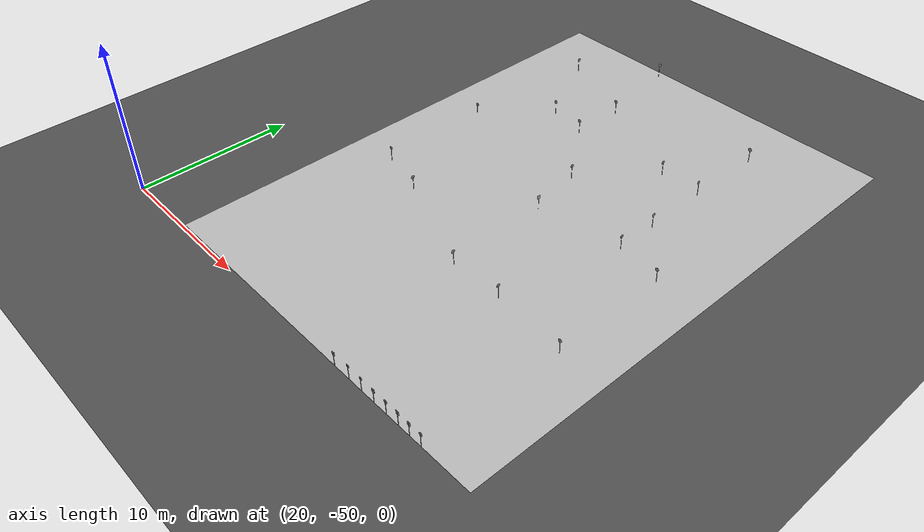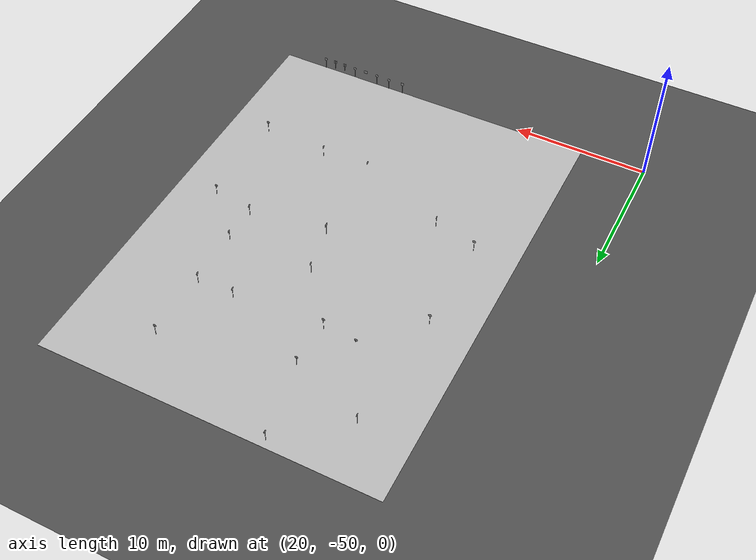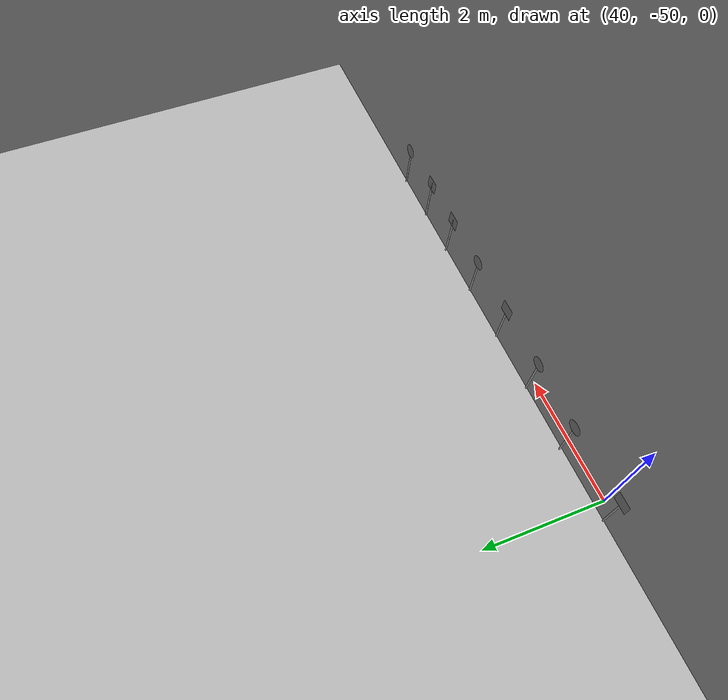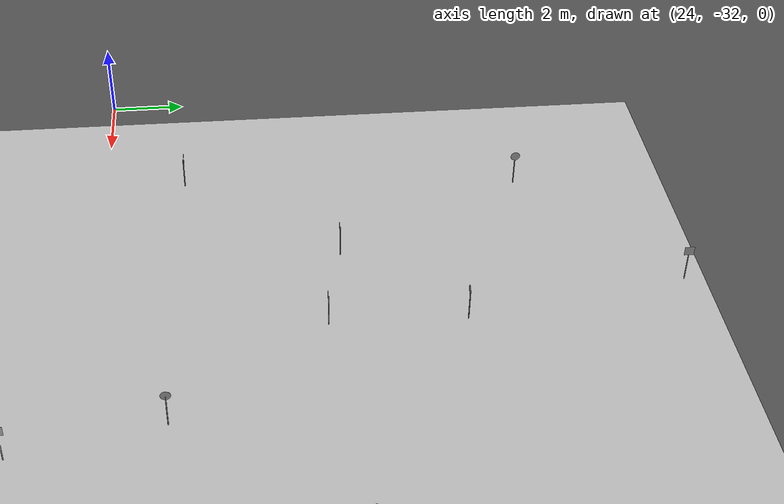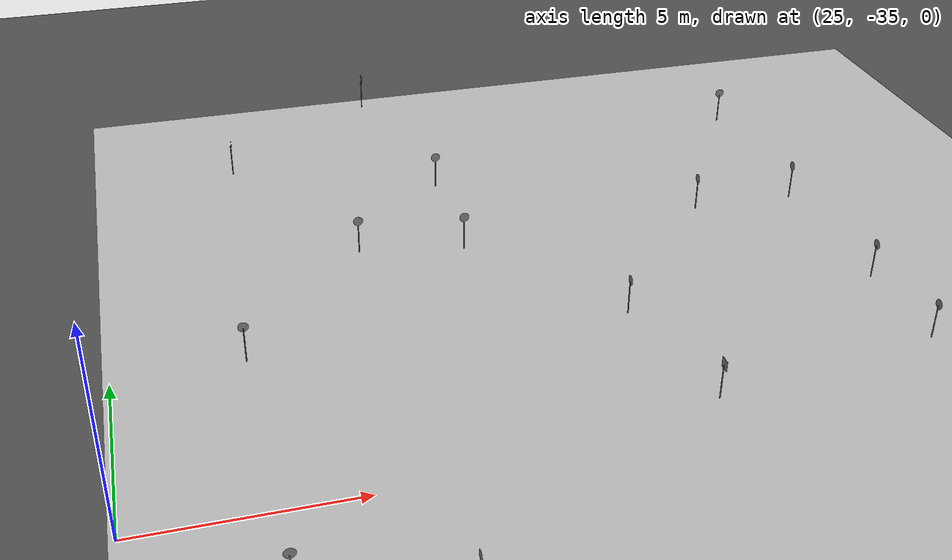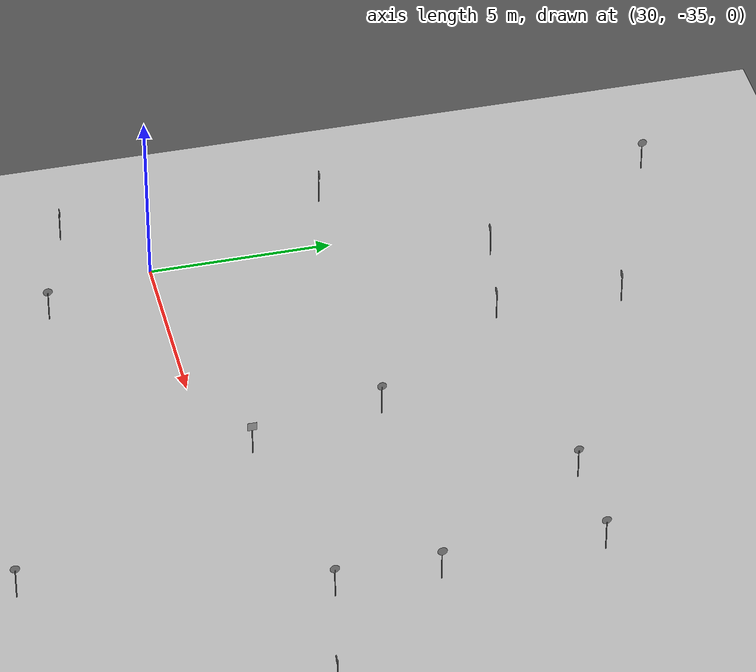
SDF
<sdf version="1.7">
 <world name="default">
  <light name="sun" type="directional">
   <pose>0 0 10 0 -0 0</pose>
   <diffuse>0.8 0.8 0.8 1</diffuse>
   <specular>0.2 0.2 0.2 1</specular>
   <attenuation>
    <range>1000</range>
    <constant>0.9</constant>
    <linear>0.01</linear>
    <quadratic>0.001</quadratic>
   </attenuation>
   <direction>-0.5 0.1 -0.9</direction>
   <spot><inner_angle>0</inner_angle><outer_angle>0</outer_angle><falloff>0</falloff></spot>
  </light>
  <model name="ground_plane">
   <static>1</static>
   <link name="link">
    <collision name="collision">
     <geometry><plane><normal>0 0 1</normal><size>100 100</size></plane></geometry>
     <surface>
      <contact><collide_bitmask>65535</collide_bitmask></contact>
      <friction><ode><mu>100</mu><mu2>50</mu2></ode></friction>
     </surface>
    </collision>
    <visual name="visual">
     <cast_shadows>0</cast_shadows>
     <geometry><plane><normal>0 0 1</normal><size>100 100</size></plane></geometry>
     <material>
      <script><uri>file://media/materials/scripts/gazebo.material</uri><name>Gazebo/DarkGrey</name></script>
     </material>
    </visual>
   </link>
  </model>
  <gravity>0 0 -9.8</gravity>
  <magnetic_field>6e-06 2.3e-05 -4.2e-05</magnetic_field>
  <atmosphere type="adiabatic"/>
  <physics type="ode">
   <max_step_size>0.001</max_step_size>
   <real_time_factor>1</real_time_factor>
   <real_time_update_rate>1000</real_time_update_rate>
  </physics>
  <scene><ambient>0.4 0.4 0.4 1</ambient><background>0.3 0.3 0.3 1</background><shadows>1</shadows></scene>
  <spherical_coordinates>
   <surface_model>EARTH_WGS84</surface_model>
   <latitude_deg>0</latitude_deg>
   <longitude_deg>0</longitude_deg>
   <elevation>0</elevation>
   <heading_deg>0</heading_deg>
  </spherical_coordinates>
  <model name="zemin3">
   <link name="link">
    <inertial>
     <mass>1</mass>
     <inertia>
      <ixx>0.166667</ixx>
      <ixy>0</ixy>
      <ixz>0</ixz>
      <iyy>0.166667</iyy>
      <iyz>0</iyz>
      <izz>0.166667</izz>
     </inertia>
    </inertial>
    <gravity>0</gravity>
    <visual name="visual">
     <geometry><box><size>25.1 33.2 0.002784</size></box></geometry>
     <material>
      <script>
       <uri>model://zemin2/materials/scripts/repeated.material</uri>
       <uri>model://zemin2/materials/textures/parkur.png</uri>
       <name>RepeatedTexture21</name>
      </script>
      <shader type="pixel"><normal_map>__default__</normal_map></shader>
      <ambient>0.18 0.204 0.212 1</ambient>
      <diffuse>0.7 0.7 0.7 1</diffuse>
      <specular>0.01 0.01 0.01 1</specular>
      <emissive>0 0 0 1</emissive>
     </material>
    </visual>
    <collision name="collision">
     <geometry><box><size>1 1 0.002784</size></box></geometry>
     <surface>
      <friction>
       <ode><mu>1</mu><mu2>1</mu2><fdir1>0 0 0</fdir1><slip1>0</slip1><slip2>0</slip2></ode>
       <torsional>
        <coefficient>1</coefficient>
        <patch_radius>0</patch_radius>
        <surface_radius>0</surface_radius>
        <use_patch_radius>1</use_patch_radius>
        <ode><slip>0</slip></ode>
       </torsional>
      </friction>
      <bounce><restitution_coefficient>0</restitution_coefficient><threshold>1e+06</threshold></bounce>
      <contact>
       <collide_without_contact>0</collide_without_contact>
       <collide_without_contact_bitmask>1</collide_without_contact_bitmask>
       <collide_bitmask>1</collide_bitmask>
       <ode>
        <soft_cfm>0</soft_cfm>
        <soft_erp>0.2</soft_erp>
        <kp>1e+13</kp>
        <kd>1</kd>
        <max_vel>0.01</max_vel>
        <min_depth>0</min_depth>
       </ode>
       <bullet>
        <split_impulse>1</split_impulse>
        <split_impulse_penetration_threshold>-0.01</split_impulse_penetration_threshold>
        <soft_cfm>0</soft_cfm>
        <soft_erp>0.2</soft_erp>
        <kp>1e+13</kp>
        <kd>1</kd>
       </bullet>
      </contact>
     </surface>
    </collision>
   </link>
   <static>1</static>
   <pose>37.3935 -33.2355 0.000289 0 -0 3.1415</pose>
  </model>
  <model name="unit_cylinder_clone">
   <pose>46.7673 -33.5895 0.449397 0.024127 0.000318 0.001365</pose>
   <link name="link">
    <inertial>
     <mass>1</mass>
     <inertia><ixx>0.145833</ixx><ixy>0</ixy><ixz>0</ixz><iyy>0.145833</iyy><iyz>0</iyz><izz>0.125</izz></inertia>
    </inertial>
    <collision name="collision">
     <geometry><cylinder><radius>0.0142338</radius><length>0.898369</length></cylinder></geometry>
    </collision>
    <visual name="visual">
     <geometry><cylinder><radius>0.0142338</radius><length>0.898369</length></cylinder></geometry>
     <material>
      <script><name>Gazebo/Grey</name><uri>file://media/materials/scripts/gazebo.material</uri></script>
     </material>
    </visual>
   </link>
  </model>
  <model name="unit_cylinder_clone_0">
   <pose>43.6163 -32.9477 0.449175 -2e-06 5e-06 0.000259</pose>
   <link name="link">
    <inertial>
     <mass>1</mass>
     <inertia><ixx>0.145833</ixx><ixy>0</ixy><ixz>0</ixz><iyy>0.145833</iyy><iyz>0</iyz><izz>0.125</izz></inertia>
    </inertial>
    <collision name="collision">
     <geometry><cylinder><radius>0.0142338</radius><length>0.898369</length></cylinder></geometry>
    </collision>
    <visual name="visual">
     <geometry><cylinder><radius>0.0142338</radius><length>0.898369</length></cylinder></geometry>
     <material>
      <script><name>Gazebo/Grey</name><uri>file://media/materials/scripts/gazebo.material</uri></script>
     </material>
    </visual>
   </link>
  </model>
  <model name="unit_cylinder_clone_1">
   <pose>43.6004 -30.2051 0.449175 -2e-06 4e-06 -6.1e-05</pose>
   <link name="link">
    <inertial>
     <mass>1</mass>
     <inertia><ixx>0.145833</ixx><ixy>0</ixy><ixz>0</ixz><iyy>0.145833</iyy><iyz>0</iyz><izz>0.125</izz></inertia>
    </inertial>
    <collision name="collision">
     <geometry><cylinder><radius>0.0142338</radius><length>0.898369</length></cylinder></geometry>
    </collision>
    <visual name="visual">
     <geometry><cylinder><radius>0.0142338</radius><length>0.898369</length></cylinder></geometry>
     <material>
      <script><name>Gazebo/Grey</name><uri>file://media/materials/scripts/gazebo.material</uri></script>
     </material>
    </visual>
   </link>
  </model>
  <model name="unit_cylinder_clone_2">
   <pose>37.8862 -33.8314 0.449175 -2e-06 -1.5e-05 -0.002672</pose>
   <link name="link">
    <inertial>
     <mass>1</mass>
     <inertia><ixx>0.145833</ixx><ixy>0</ixy><ixz>0</ixz><iyy>0.145833</iyy><iyz>0</iyz><izz>0.125</izz></inertia>
    </inertial>
    <collision name="collision">
     <geometry><cylinder><radius>0.0142338</radius><length>0.898369</length></cylinder></geometry>
    </collision>
    <visual name="visual">
     <geometry><cylinder><radius>0.0142338</radius><length>0.898369</length></cylinder></geometry>
     <material>
      <script><name>Gazebo/Grey</name><uri>file://media/materials/scripts/gazebo.material</uri></script>
     </material>
    </visual>
   </link>
  </model>
  <model name="unit_cylinder_clone_3">
   <pose>37.1194 -30.2194 0.449191 0 -0.000482 -0.000117</pose>
   <link name="link">
    <inertial>
     <mass>1</mass>
     <inertia><ixx>0.145833</ixx><ixy>0</ixy><ixz>0</ixz><iyy>0.145833</iyy><iyz>0</iyz><izz>0.125</izz></inertia>
    </inertial>
    <collision name="collision">
     <geometry><cylinder><radius>0.0142338</radius><length>0.898369</length></cylinder></geometry>
    </collision>
    <visual name="visual">
     <geometry><cylinder><radius>0.0142338</radius><length>0.898369</length></cylinder></geometry>
     <material>
      <script><name>Gazebo/Grey</name><uri>file://media/materials/scripts/gazebo.material</uri></script>
     </material>
    </visual>
   </link>
  </model>
  <model name="unit_cylinder_clone_4">
   <pose>34.062 -26.3375 0.449185 -6e-06 -3.3e-05 0.000201</pose>
   <link name="link">
    <inertial>
     <mass>1</mass>
     <inertia><ixx>0.145833</ixx><ixy>0</ixy><ixz>0</ixz><iyy>0.145833</iyy><iyz>0</iyz><izz>0.125</izz></inertia>
    </inertial>
    <collision name="collision">
     <geometry><cylinder><radius>0.0142338</radius><length>0.898369</length></cylinder></geometry>
    </collision>
    <visual name="visual">
     <geometry><cylinder><radius>0.0142338</radius><length>0.898369</length></cylinder></geometry>
     <material>
      <script><name>Gazebo/Grey</name><uri>file://media/materials/scripts/gazebo.material</uri></script>
     </material>
    </visual>
   </link>
  </model>
  <model name="unit_cylinder_clone_5">
   <pose>31.4011 -25.8279 0.449185 -2e-06 -1.7e-05 -0.000363</pose>
   <link name="link">
    <inertial>
     <mass>1</mass>
     <inertia><ixx>0.145833</ixx><ixy>0</ixy><ixz>0</ixz><iyy>0.145833</iyy><iyz>0</iyz><izz>0.125</izz></inertia>
    </inertial>
    <collision name="collision">
     <geometry><cylinder><radius>0.0142338</radius><length>0.898369</length></cylinder></geometry>
    </collision>
    <visual name="visual">
     <geometry><cylinder><radius>0.0142338</radius><length>0.898369</length></cylinder></geometry>
     <material>
      <script><name>Gazebo/Grey</name><uri>file://media/materials/scripts/gazebo.material</uri></script>
     </material>
    </visual>
   </link>
  </model>
  <model name="unit_cylinder_clone_6">
   <pose>40.7163 -25.8872 0.449184 6e-06 -1.1e-05 0.000217</pose>
   <link name="link">
    <inertial>
     <mass>1</mass>
     <inertia><ixx>0.145833</ixx><ixy>0</ixy><ixz>0</ixz><iyy>0.145833</iyy><iyz>0</iyz><izz>0.125</izz></inertia>
    </inertial>
    <collision name="collision">
     <geometry><cylinder><radius>0.0142338</radius><length>0.898369</length></cylinder></geometry>
    </collision>
    <visual name="visual">
     <geometry><cylinder><radius>0.0142338</radius><length>0.898369</length></cylinder></geometry>
     <material>
      <script><name>Gazebo/Grey</name><uri>file://media/materials/scripts/gazebo.material</uri></script>
     </material>
    </visual>
   </link>
  </model>
  <model name="unit_cylinder_clone_7">
   <pose>43.4968 -25.9178 0.449184 -3e-06 -5e-06 0.000288</pose>
   <link name="link">
    <inertial>
     <mass>1</mass>
     <inertia><ixx>0.145833</ixx><ixy>0</ixy><ixz>0</ixz><iyy>0.145833</iyy><iyz>0</iyz><izz>0.125</izz></inertia>
    </inertial>
    <collision name="collision">
     <geometry><cylinder><radius>0.0142338</radius><length>0.898369</length></cylinder></geometry>
    </collision>
    <visual name="visual">
     <geometry><cylinder><radius>0.0142338</radius><length>0.898369</length></cylinder></geometry>
     <material>
      <script><name>Gazebo/Grey</name><uri>file://media/materials/scripts/gazebo.material</uri></script>
     </material>
    </visual>
   </link>
  </model>
  <model name="unit_cylinder_clone_8">
   <pose>34.1327 -22.8852 0.449175 -2e-06 5e-06 0.001184</pose>
   <link name="link">
    <inertial>
     <mass>1</mass>
     <inertia><ixx>0.145833</ixx><ixy>0</ixy><ixz>0</ixz><iyy>0.145833</iyy><iyz>0</iyz><izz>0.125</izz></inertia>
    </inertial>
    <collision name="collision">
     <geometry><cylinder><radius>0.0142338</radius><length>0.898369</length></cylinder></geometry>
    </collision>
    <visual name="visual">
     <geometry><cylinder><radius>0.0142338</radius><length>0.898369</length></cylinder></geometry>
     <material>
      <script><name>Gazebo/Grey</name><uri>file://media/materials/scripts/gazebo.material</uri></script>
     </material>
    </visual>
   </link>
  </model>
  <model name="unit_cylinder_clone_10">
   <pose>43.574 -20.8977 0.449184 -5e-06 1.2e-05 4.4e-05</pose>
   <link name="link">
    <inertial>
     <mass>1</mass>
     <inertia><ixx>0.145833</ixx><ixy>0</ixy><ixz>0</ixz><iyy>0.145833</iyy><iyz>0</iyz><izz>0.125</izz></inertia>
    </inertial>
    <collision name="collision">
     <geometry><cylinder><radius>0.0142338</radius><length>0.898369</length></cylinder></geometry>
    </collision>
    <visual name="visual">
     <geometry><cylinder><radius>0.0142338</radius><length>0.898369</length></cylinder></geometry>
     <material>
      <script><name>Gazebo/Grey</name><uri>file://media/materials/scripts/gazebo.material</uri></script>
     </material>
    </visual>
   </link>
  </model>
  <model name="unit_cylinder_clone_11">
   <pose>33.0941 -17.1688 0.449175 -2e-06 4e-06 6e-06</pose>
   <link name="link">
    <inertial>
     <mass>1</mass>
     <inertia><ixx>0.145833</ixx><ixy>0</ixy><ixz>0</ixz><iyy>0.145833</iyy><iyz>0</iyz><izz>0.125</izz></inertia>
    </inertial>
    <collision name="collision">
     <geometry><cylinder><radius>0.0142338</radius><length>0.898369</length></cylinder></geometry>
    </collision>
    <visual name="visual">
     <geometry><cylinder><radius>0.0142338</radius><length>0.898369</length></cylinder></geometry>
     <material>
      <script><name>Gazebo/Grey</name><uri>file://media/materials/scripts/gazebo.material</uri></script>
     </material>
    </visual>
   </link>
  </model>
  <model name="unit_cylinder_clone_12">
   <pose>28.6831 -20.7845 0.487892 0 -0 0</pose>
   <link name="link">
    <inertial>
     <mass>1</mass>
     <inertia><ixx>0.145833</ixx><ixy>0</ixy><ixz>0</ixz><iyy>0.145833</iyy><iyz>0</iyz><izz>0.125</izz></inertia>
    </inertial>
    <collision name="collision">
     <geometry><cylinder><radius>0.0142338</radius><length>0.898369</length></cylinder></geometry>
    </collision>
    <visual name="visual">
     <geometry><cylinder><radius>0.0142338</radius><length>0.898369</length></cylinder></geometry>
     <material>
      <script><name>Gazebo/Grey</name><uri>file://media/materials/scripts/gazebo.material</uri></script>
     </material>
    </visual>
   </link>
  </model>
  <model name="unit_cylinder_clone_13">
   <pose>28.0437 -29.8735 0.449184 -2e-06 -2e-06 0.000338</pose>
   <link name="link">
    <inertial>
     <mass>1</mass>
     <inertia><ixx>0.145833</ixx><ixy>0</ixy><ixz>0</ixz><iyy>0.145833</iyy><iyz>0</iyz><izz>0.125</izz></inertia>
    </inertial>
    <collision name="collision">
     <geometry><cylinder><radius>0.0142338</radius><length>0.898369</length></cylinder></geometry>
    </collision>
    <visual name="visual">
     <geometry><cylinder><radius>0.0142338</radius><length>0.898369</length></cylinder></geometry>
     <material>
      <script><name>Gazebo/Grey</name><uri>file://media/materials/scripts/gazebo.material</uri></script>
     </material>
    </visual>
   </link>
  </model>
  <model name="unit_cylinder_clone_14">
   <pose>28.0675 -37.1359 0.449175 -2e-06 7e-06 0.000323</pose>
   <link name="link">
    <inertial>
     <mass>1</mass>
     <inertia><ixx>0.145833</ixx><ixy>0</ixy><ixz>0</ixz><iyy>0.145833</iyy><iyz>0</iyz><izz>0.125</izz></inertia>
    </inertial>
    <collision name="collision">
     <geometry><cylinder><radius>0.0142338</radius><length>0.898369</length></cylinder></geometry>
    </collision>
    <visual name="visual">
     <geometry><cylinder><radius>0.0142338</radius><length>0.898369</length></cylinder></geometry>
     <material>
      <script><name>Gazebo/Grey</name><uri>file://media/materials/scripts/gazebo.material</uri></script>
     </material>
    </visual>
   </link>
  </model>
  <model name="unit_cylinder_clone_15">
   <pose>31.3524 -38.0203 0.449175 7e-06 1.7e-05 6.9e-05</pose>
   <link name="link">
    <inertial>
     <mass>1</mass>
     <inertia><ixx>0.145833</ixx><ixy>0</ixy><ixz>0</ixz><iyy>0.145833</iyy><iyz>0</iyz><izz>0.125</izz></inertia>
    </inertial>
    <collision name="collision">
     <geometry><cylinder><radius>0.0142338</radius><length>0.898369</length></cylinder></geometry>
    </collision>
    <visual name="visual">
     <geometry><cylinder><radius>0.0142338</radius><length>0.898369</length></cylinder></geometry>
     <material>
      <script><name>Gazebo/Grey</name><uri>file://media/materials/scripts/gazebo.material</uri></script>
     </material>
    </visual>
   </link>
  </model>
  <model name="unit_cylinder_clone_16">
   <pose>38.1583 -40.6647 0.449185 -4e-06 1.5e-05 -6.8e-05</pose>
   <link name="link">
    <inertial>
     <mass>1</mass>
     <inertia><ixx>0.145833</ixx><ixy>0</ixy><ixz>0</ixz><iyy>0.145833</iyy><iyz>0</iyz><izz>0.125</izz></inertia>
    </inertial>
    <collision name="collision">
     <geometry><cylinder><radius>0.0142338</radius><length>0.898369</length></cylinder></geometry>
    </collision>
    <visual name="visual">
     <geometry><cylinder><radius>0.0142338</radius><length>0.898369</length></cylinder></geometry>
     <material>
      <script><name>Gazebo/Grey</name><uri>file://media/materials/scripts/gazebo.material</uri></script>
     </material>
    </visual>
   </link>
  </model>
  <model name="unit_cylinder_clone_17">
   <pose>41.8374 -40.6802 0.449395 -0.005891 -0.001828 -0.009199</pose>
   <link name="link">
    <inertial>
     <mass>1</mass>
     <inertia><ixx>0.145833</ixx><ixy>0</ixy><ixz>0</ixz><iyy>0.145833</iyy><iyz>0</iyz><izz>0.125</izz></inertia>
    </inertial>
    <collision name="collision">
     <geometry><cylinder><radius>0.0142338</radius><length>0.898369</length></cylinder></geometry>
    </collision>
    <visual name="visual">
     <geometry><cylinder><radius>0.0142338</radius><length>0.898369</length></cylinder></geometry>
     <material>
      <script><name>Gazebo/Grey</name><uri>file://media/materials/scripts/gazebo.material</uri></script>
     </material>
    </visual>
   </link>
  </model>
  <model name="unit_cylinder_clone_clone_0">
   <pose>46.829 -41.1296 0.449189 -0.000299 2.5e-05 4.9e-05</pose>
   <link name="link">
    <inertial>
     <mass>1</mass>
     <inertia><ixx>0.145833</ixx><ixy>0</ixy><ixz>0</ixz><iyy>0.145833</iyy><iyz>0</iyz><izz>0.125</izz></inertia>
    </inertial>
    <collision name="collision">
     <geometry><cylinder><radius>0.0142338</radius><length>0.898369</length></cylinder></geometry>
    </collision>
    <visual name="visual">
     <geometry><cylinder><radius>0.0142338</radius><length>0.898369</length></cylinder></geometry>
     <material>
      <script><name>Gazebo/Grey</name><uri>file://media/materials/scripts/gazebo.material</uri></script>
     </material>
    </visual>
   </link>
  </model>
  <model name="sagadonulmezz">
   <link name="link">
    <inertial>
     <mass>0.00065094</mass>
     <inertia>
      <ixx>3.39e-06</ixx>
      <ixy>0</ixy>
      <ixz>0</ixz>
      <iyy>6.78e-06</iyy>
      <iyz>0</iyz>
      <izz>3.39e-06</izz>
     </inertia>
    </inertial>
    <gravity>0</gravity>
    <visual name="visual">
     <geometry><box><size>0.25 0.000344 0.25</size></box></geometry>
     <material>
      <script>
       <uri>model://sagadonulmezz/materials/scripts/repeated.material</uri>
       <uri>model://sagadonulmezz/materials/textures/sagadonulmez.png</uri>
       <name>RepeatedTexture24</name>
      </script>
      <shader type="pixel"><normal_map>__default__</normal_map></shader>
      <ambient>0 0 0 1</ambient>
      <diffuse>0.7 0.7 0.7 1</diffuse>
      <specular>0.01 0.01 0.01 1</specular>
      <emissive>0.694 0.694 0.694 1</emissive>
      <lighting>0</lighting>
     </material>
     <transparency>1</transparency>
    </visual>
    <collision name="collision">
     <geometry><box><size>0.25 5.3e-05 0.25</size></box></geometry>
     <surface>
      <friction>
       <ode><mu>1</mu><mu2>1</mu2><fdir1>0 0 0</fdir1><slip1>0</slip1><slip2>0</slip2></ode>
       <torsional>
        <coefficient>1</coefficient>
        <patch_radius>0</patch_radius>
        <surface_radius>0</surface_radius>
        <use_patch_radius>1</use_patch_radius>
        <ode><slip>0</slip></ode>
       </torsional>
      </friction>
      <bounce><restitution_coefficient>0</restitution_coefficient><threshold>1e+06</threshold></bounce>
      <contact>
       <collide_without_contact>0</collide_without_contact>
       <collide_without_contact_bitmask>1</collide_without_contact_bitmask>
       <collide_bitmask>1</collide_bitmask>
       <ode>
        <soft_cfm>0</soft_cfm>
        <soft_erp>0.2</soft_erp>
        <kp>1e+13</kp>
        <kd>1</kd>
        <max_vel>0.01</max_vel>
        <min_depth>0</min_depth>
       </ode>
       <bullet>
        <split_impulse>1</split_impulse>
        <split_impulse_penetration_threshold>-0.01</split_impulse_penetration_threshold>
        <soft_cfm>0</soft_cfm>
        <soft_erp>0.2</soft_erp>
        <kp>1e+13</kp>
        <kd>1</kd>
       </bullet>
      </contact>
     </surface>
    </collision>
   </link>
   <static>1</static>
   <pose>43.6177 -30.1961 0.925 0 0 -1.57552</pose>
  </model>
  <model name="durak3">
   <link name="link_clone">
    <inertial>
     <mass>0.00526726</mass>
     <inertia>
      <ixx>0.00043895</ixx>
      <ixy>0</ixy>
      <ixz>0</ixz>
      <iyy>0.00087788</iyy>
      <iyz>0</iyz>
      <izz>0.00043895</izz>
     </inertia>
    </inertial>
    <pose>-2.04579 1.48415 0.646979 0 -0 0</pose>
    <gravity>0</gravity>
    <visual name="visual">
     <geometry><box><size>0.25 0.0001 0.25</size></box></geometry>
     <material>
      <script>
       <uri>model://durak2/materials/textures/durak.png</uri>
       <uri>model://durak2/materials/scripts/repeated.material</uri>
       <name>RepeatedTexture3</name>
      </script>
      <shader type="pixel"><normal_map>__default__</normal_map></shader>
      <lighting>0</lighting>
      <emissive>0 0 0 1</emissive>
     </material>
    </visual>
    <collision name="collision">
     <geometry><box><size>0.25 0.0001 0.25</size></box></geometry>
     <surface>
      <friction>
       <ode><mu>1</mu><mu2>1</mu2><fdir1>0 0 0</fdir1><slip1>0</slip1><slip2>0</slip2></ode>
       <torsional>
        <coefficient>1</coefficient>
        <patch_radius>0</patch_radius>
        <surface_radius>0</surface_radius>
        <use_patch_radius>1</use_patch_radius>
        <ode><slip>0</slip></ode>
       </torsional>
      </friction>
      <bounce><restitution_coefficient>0</restitution_coefficient><threshold>1e+06</threshold></bounce>
      <contact>
       <collide_without_contact>0</collide_without_contact>
       <collide_without_contact_bitmask>1</collide_without_contact_bitmask>
       <collide_bitmask>1</collide_bitmask>
       <ode>
        <soft_cfm>0</soft_cfm>
        <soft_erp>0.2</soft_erp>
        <kp>1e+13</kp>
        <kd>1</kd>
        <max_vel>0.01</max_vel>
        <min_depth>0</min_depth>
       </ode>
       <bullet>
        <split_impulse>1</split_impulse>
        <split_impulse_penetration_threshold>-0.01</split_impulse_penetration_threshold>
        <soft_cfm>0</soft_cfm>
        <soft_erp>0.2</soft_erp>
        <kp>1e+13</kp>
        <kd>1</kd>
       </bullet>
      </contact>
     </surface>
    </collision>
   </link>
   <static>1</static>
   <pose>39.3903 -31.7832 0.267654 0 -0 1.5708</pose>
  </model>
  <model name="sagadon">
   <link name="link_clone">
    <inertial>
     <mass>0.199386</mass>
     <inertia>
      <ixx>0.0166156</ixx>
      <ixy>0</ixy>
      <ixz>0</ixz>
      <iyy>0.0332311</iyy>
      <iyz>0</iyz>
      <izz>0.0166156</izz>
     </inertia>
    </inertial>
    <pose>-0.153624 1.8463 0.781019 0 -0 0</pose>
    <gravity>0</gravity>
    <visual name="visual">
     <geometry><box><size>0.25 0.001364 0.25</size></box></geometry>
     <material>
      <script>
       <uri>model://sagadon/materials/scripts/sagadon.material</uri>
       <uri>model://sagadon/materials/textures/sagadon.png</uri>
       <name>RepeatedTexture15</name>
      </script>
      <shader type="pixel"><normal_map>__default__</normal_map></shader>
      <ambient>0 0 0 1</ambient>
      <diffuse>0.7 0.7 0.7 1</diffuse>
      <specular>0.01 0.01 0.01 1</specular>
      <emissive>0 0 0 1</emissive>
      <lighting>0</lighting>
     </material>
     <transparency>1</transparency>
    </visual>
    <collision name="collision">
     <geometry><box><size>0.25 0.0001 0.25</size></box></geometry>
     <surface>
      <friction>
       <ode><mu>1</mu><mu2>1</mu2><fdir1>0 0 0</fdir1><slip1>0</slip1><slip2>0</slip2></ode>
       <torsional>
        <coefficient>1</coefficient>
        <patch_radius>0</patch_radius>
        <surface_radius>0</surface_radius>
        <use_patch_radius>1</use_patch_radius>
        <ode><slip>0</slip></ode>
       </torsional>
      </friction>
      <bounce><restitution_coefficient>0</restitution_coefficient><threshold>1e+06</threshold></bounce>
      <contact>
       <collide_without_contact>0</collide_without_contact>
       <collide_without_contact_bitmask>1</collide_without_contact_bitmask>
       <collide_bitmask>1</collide_bitmask>
       <ode>
        <soft_cfm>0</soft_cfm>
        <soft_erp>0.2</soft_erp>
        <kp>1e+13</kp>
        <kd>1</kd>
        <max_vel>0.01</max_vel>
        <min_depth>0</min_depth>
       </ode>
       <bullet>
        <split_impulse>1</split_impulse>
        <split_impulse_penetration_threshold>-0.01</split_impulse_penetration_threshold>
        <soft_cfm>0</soft_cfm>
        <soft_erp>0.2</soft_erp>
        <kp>1e+13</kp>
        <kd>1</kd>
       </bullet>
      </contact>
     </surface>
    </collision>
   </link>
   <static>1</static>
   <pose>38.9798 -30.0619 0.145331 0 -0 1.5708</pose>
  </model>
  <model name="sagadon_0">
   <link name="link_clone">
    <inertial>
     <mass>0.199386</mass>
     <inertia>
      <ixx>0.0166156</ixx>
      <ixy>0</ixy>
      <ixz>0</ixz>
      <iyy>0.0332311</iyy>
      <iyz>0</iyz>
      <izz>0.0166156</izz>
     </inertia>
    </inertial>
    <pose>-0.153624 1.8463 0.781019 0 -0 0</pose>
    <gravity>0</gravity>
    <visual name="visual">
     <geometry><box><size>0.25 0.001364 0.25</size></box></geometry>
     <material>
      <script>
       <uri>model://sagadon/materials/scripts/sagadon.material</uri>
       <uri>model://sagadon/materials/textures/sagadon.png</uri>
       <name>RepeatedTexture15</name>
      </script>
      <shader type="pixel"><normal_map>__default__</normal_map></shader>
      <ambient>0 0 0 1</ambient>
      <diffuse>0.7 0.7 0.7 1</diffuse>
      <specular>0.01 0.01 0.01 1</specular>
      <emissive>0 0 0 1</emissive>
      <lighting>0</lighting>
     </material>
     <transparency>1</transparency>
    </visual>
    <collision name="collision">
     <geometry><box><size>0.25 0.0001 0.25</size></box></geometry>
     <surface>
      <friction>
       <ode><mu>1</mu><mu2>1</mu2><fdir1>0 0 0</fdir1><slip1>0</slip1><slip2>0</slip2></ode>
       <torsional>
        <coefficient>1</coefficient>
        <patch_radius>0</patch_radius>
        <surface_radius>0</surface_radius>
        <use_patch_radius>1</use_patch_radius>
        <ode><slip>0</slip></ode>
       </torsional>
      </friction>
      <bounce><restitution_coefficient>0</restitution_coefficient><threshold>1e+06</threshold></bounce>
      <contact>
       <collide_without_contact>0</collide_without_contact>
       <collide_without_contact_bitmask>1</collide_without_contact_bitmask>
       <collide_bitmask>1</collide_bitmask>
       <ode>
        <soft_cfm>0</soft_cfm>
        <soft_erp>0.2</soft_erp>
        <kp>1e+13</kp>
        <kd>1</kd>
        <max_vel>0.01</max_vel>
        <min_depth>0</min_depth>
       </ode>
       <bullet>
        <split_impulse>1</split_impulse>
        <split_impulse_penetration_threshold>-0.01</split_impulse_penetration_threshold>
        <soft_cfm>0</soft_cfm>
        <soft_erp>0.2</soft_erp>
        <kp>1e+13</kp>
        <kd>1</kd>
       </bullet>
      </contact>
     </surface>
    </collision>
   </link>
   <static>1</static>
   <pose>34.2206 -28.1998 0.153138 0 -0 0</pose>
  </model>
  <model name="soladonulmez">
   <link name="link">
    <inertial>
     <mass>0.0029489</mass>
     <inertia>
      <ixx>1.53589e-05</ixx>
      <ixy>0</ixy>
      <ixz>0</ixz>
      <iyy>3.07177e-05</iyy>
      <iyz>0</iyz>
      <izz>1.53589e-05</izz>
     </inertia>
    </inertial>
    <gravity>0</gravity>
    <visual name="visual">
     <geometry><box><size>0.25 1.3e-05 0.25</size></box></geometry>
     <material>
      <script>
       <uri>model://ornekkare/materials/scripts/repeated.material</uri>
       <uri>model://ornekkare/materials/textures/soladonulmezz.png</uri>
       <name>RepeatedTexture9</name>
      </script>
      <shader type="pixel"><normal_map>__default__</normal_map></shader>
      <ambient>0 0 0 1</ambient>
      <diffuse>0.7 0.7 0.7 1</diffuse>
      <specular>0.01 0.01 0.01 1</specular>
      <emissive>0.694 0.694 0.694 1</emissive>
      <lighting>0</lighting>
     </material>
     <transparency>1</transparency>
    </visual>
    <collision name="collision">
     <geometry><box><size>0.25 0.00011 0.25</size></box></geometry>
     <surface>
      <friction>
       <ode><mu>1</mu><mu2>1</mu2><fdir1>0 0 0</fdir1><slip1>0</slip1><slip2>0</slip2></ode>
       <torsional>
        <coefficient>1</coefficient>
        <patch_radius>0</patch_radius>
        <surface_radius>0</surface_radius>
        <use_patch_radius>1</use_patch_radius>
        <ode><slip>0</slip></ode>
       </torsional>
      </friction>
      <bounce><restitution_coefficient>0</restitution_coefficient><threshold>1e+06</threshold></bounce>
      <contact>
       <collide_without_contact>0</collide_without_contact>
       <collide_without_contact_bitmask>1</collide_without_contact_bitmask>
       <collide_bitmask>1</collide_bitmask>
       <ode>
        <soft_cfm>0</soft_cfm>
        <soft_erp>0.2</soft_erp>
        <kp>1e+13</kp>
        <kd>1</kd>
        <max_vel>0.01</max_vel>
        <min_depth>0</min_depth>
       </ode>
       <bullet>
        <split_impulse>1</split_impulse>
        <split_impulse_penetration_threshold>-0.01</split_impulse_penetration_threshold>
        <soft_cfm>0</soft_cfm>
        <soft_erp>0.2</soft_erp>
        <kp>1e+13</kp>
        <kd>1</kd>
       </bullet>
      </contact>
     </surface>
    </collision>
   </link>
   <static>1</static>
   <pose>46.8411 -41.1451 0.925 0 -0 0</pose>
  </model>
  <model name="soladon">
   <link name="link_clone">
    <inertial>
     <mass>0.0435615</mass>
     <inertia>
      <ixx>0.00363012</ixx>
      <ixy>0</ixy>
      <ixz>0</ixz>
      <iyy>0.00726024</iyy>
      <iyz>0</iyz>
      <izz>0.00363012</izz>
     </inertia>
    </inertial>
    <pose>-0.747635 1.04083 0.781019 0 -0 0</pose>
    <gravity>0</gravity>
    <visual name="visual">
     <geometry><box><size>0.25 0.000308 0.25</size></box></geometry>
     <material>
      <script>
       <uri>model://soladon/materials/scripts/soladon.material</uri>
       <uri>model://soladon/materials/textures/soladon.png</uri>
       <name>RepeatedTexture14</name>
      </script>
      <shader type="pixel"><normal_map>__default__</normal_map></shader>
      <ambient>0 0 0 1</ambient>
      <diffuse>0.7 0.7 0.7 1</diffuse>
      <specular>0.01 0.01 0.01 1</specular>
      <emissive>0 0 0 1</emissive>
      <lighting>0</lighting>
     </material>
     <transparency>1</transparency>
    </visual>
    <collision name="collision">
     <geometry><box><size>0.25 0.0001 0.25</size></box></geometry>
     <surface>
      <friction>
       <ode><mu>1</mu><mu2>1</mu2><fdir1>0 0 0</fdir1><slip1>0</slip1><slip2>0</slip2></ode>
       <torsional>
        <coefficient>1</coefficient>
        <patch_radius>0</patch_radius>
        <surface_radius>0</surface_radius>
        <use_patch_radius>1</use_patch_radius>
        <ode><slip>0</slip></ode>
       </torsional>
      </friction>
      <bounce><restitution_coefficient>0</restitution_coefficient><threshold>1e+06</threshold></bounce>
      <contact>
       <collide_without_contact>0</collide_without_contact>
       <collide_without_contact_bitmask>1</collide_without_contact_bitmask>
       <collide_bitmask>1</collide_bitmask>
       <ode>
        <soft_cfm>0</soft_cfm>
        <soft_erp>0.2</soft_erp>
        <kp>1e+13</kp>
        <kd>1</kd>
        <max_vel>0.01</max_vel>
        <min_depth>0</min_depth>
       </ode>
       <bullet>
        <split_impulse>1</split_impulse>
        <split_impulse_penetration_threshold>-0.01</split_impulse_penetration_threshold>
        <soft_cfm>0</soft_cfm>
        <soft_erp>0.2</soft_erp>
        <kp>1e+13</kp>
        <kd>1</kd>
       </bullet>
      </contact>
     </surface>
    </collision>
   </link>
   <static>1</static>
   <pose>47.5093 -34.6626 0.130865 0 -0 0</pose>
  </model>
  <model name="soladonulmez_0">
   <link name="link">
    <inertial>
     <mass>0.0029489</mass>
     <inertia>
      <ixx>1.53589e-05</ixx>
      <ixy>0</ixy>
      <ixz>0</ixz>
      <iyy>3.07177e-05</iyy>
      <iyz>0</iyz>
      <izz>1.53589e-05</izz>
     </inertia>
    </inertial>
    <gravity>0</gravity>
    <visual name="visual">
     <geometry><box><size>0.25 1.3e-05 0.25</size></box></geometry>
     <material>
      <script>
       <uri>model://ornekkare/materials/scripts/repeated.material</uri>
       <uri>model://ornekkare/materials/textures/soladonulmezz.png</uri>
       <name>RepeatedTexture9</name>
      </script>
      <shader type="pixel"><normal_map>__default__</normal_map></shader>
      <ambient>0 0 0 1</ambient>
      <diffuse>0.7 0.7 0.7 1</diffuse>
      <specular>0.01 0.01 0.01 1</specular>
      <emissive>0.694 0.694 0.694 1</emissive>
      <lighting>0</lighting>
     </material>
     <transparency>1</transparency>
    </visual>
    <collision name="collision">
     <geometry><box><size>0.25 0.00011 0.25</size></box></geometry>
     <surface>
      <friction>
       <ode><mu>1</mu><mu2>1</mu2><fdir1>0 0 0</fdir1><slip1>0</slip1><slip2>0</slip2></ode>
       <torsional>
        <coefficient>1</coefficient>
        <patch_radius>0</patch_radius>
        <surface_radius>0</surface_radius>
        <use_patch_radius>1</use_patch_radius>
        <ode><slip>0</slip></ode>
       </torsional>
      </friction>
      <bounce><restitution_coefficient>0</restitution_coefficient><threshold>1e+06</threshold></bounce>
      <contact>
       <collide_without_contact>0</collide_without_contact>
       <collide_without_contact_bitmask>1</collide_without_contact_bitmask>
       <collide_bitmask>1</collide_bitmask>
       <ode>
        <soft_cfm>0</soft_cfm>
        <soft_erp>0.2</soft_erp>
        <kp>1e+13</kp>
        <kd>1</kd>
        <max_vel>0.01</max_vel>
        <min_depth>0</min_depth>
       </ode>
       <bullet>
        <split_impulse>1</split_impulse>
        <split_impulse_penetration_threshold>-0.01</split_impulse_penetration_threshold>
        <soft_cfm>0</soft_cfm>
        <soft_erp>0.2</soft_erp>
        <kp>1e+13</kp>
        <kd>1</kd>
       </bullet>
      </contact>
     </surface>
    </collision>
   </link>
   <static>1</static>
   <pose>43.6318 -32.9518 0.925 0 -0 1.5708</pose>
  </model>
  <model name="soladonulmez_clone">
   <link name="link">
    <inertial>
     <mass>0.0029489</mass>
     <inertia>
      <ixx>1.53589e-05</ixx>
      <ixy>0</ixy>
      <ixz>0</ixz>
      <iyy>3.07177e-05</iyy>
      <iyz>0</iyz>
      <izz>1.53589e-05</izz>
     </inertia>
    </inertial>
    <gravity>0</gravity>
    <visual name="visual">
     <geometry><box><size>0.25 1.3e-05 0.25</size></box></geometry>
     <material>
      <script>
       <uri>model://ornekkare/materials/scripts/repeated.material</uri>
       <uri>model://ornekkare/materials/textures/soladonulmezz.png</uri>
       <name>RepeatedTexture9</name>
      </script>
      <shader type="pixel"><normal_map>__default__</normal_map></shader>
      <ambient>0 0 0 1</ambient>
      <diffuse>0.7 0.7 0.7 1</diffuse>
      <specular>0.01 0.01 0.01 1</specular>
      <emissive>0.694 0.694 0.694 1</emissive>
      <lighting>0</lighting>
     </material>
     <transparency>1</transparency>
    </visual>
    <collision name="collision">
     <geometry><box><size>0.25 0.00011 0.25</size></box></geometry>
     <surface>
      <friction>
       <ode><mu>1</mu><mu2>1</mu2><fdir1>0 0 0</fdir1><slip1>0</slip1><slip2>0</slip2></ode>
       <torsional>
        <coefficient>1</coefficient>
        <patch_radius>0</patch_radius>
        <surface_radius>0</surface_radius>
        <use_patch_radius>1</use_patch_radius>
        <ode><slip>0</slip></ode>
       </torsional>
      </friction>
      <bounce><restitution_coefficient>0</restitution_coefficient><threshold>1e+06</threshold></bounce>
      <contact>
       <collide_without_contact>0</collide_without_contact>
       <collide_without_contact_bitmask>1</collide_without_contact_bitmask>
       <collide_bitmask>1</collide_bitmask>
       <ode>
        <soft_cfm>0</soft_cfm>
        <soft_erp>0.2</soft_erp>
        <kp>1e+13</kp>
        <kd>1</kd>
        <max_vel>0.01</max_vel>
        <min_depth>0</min_depth>
       </ode>
       <bullet>
        <split_impulse>1</split_impulse>
        <split_impulse_penetration_threshold>-0.01</split_impulse_penetration_threshold>
        <soft_cfm>0</soft_cfm>
        <soft_erp>0.2</soft_erp>
        <kp>1e+13</kp>
        <kd>1</kd>
       </bullet>
      </contact>
     </surface>
    </collision>
   </link>
   <static>1</static>
   <pose>31.4047 -25.8484 0.925 0 -0 0</pose>
  </model>
  <model name="girisiolmayan">
   <link name="link">
    <inertial>
     <mass>0.00037176</mass>
     <inertia>
      <ixx>3.098e-05</ixx>
      <ixy>0</ixy>
      <ixz>0</ixz>
      <iyy>6.196e-05</iyy>
      <iyz>0</iyz>
      <izz>3.098e-05</izz>
     </inertia>
    </inertial>
    <pose>0 0 0.852536 0 -0 0</pose>
    <gravity>0</gravity>
    <visual name="visual">
     <geometry><box><size>0.25 0.0001 0.25</size></box></geometry>
     <material>
      <script>
       <uri>model://ornek/materials/scripts/repeated.material</uri>
       <uri>model://ornek/materials/textures/girisiolmayan.png</uri>
       <name>RepeatedTexture10</name>
      </script>
      <shader type="pixel"><normal_map>__default__</normal_map></shader>
      <lighting>0</lighting>
      <emissive>0 0 0 1</emissive>
     </material>
     <transparency>1</transparency>
    </visual>
    <collision name="collision">
     <geometry><box><size>1 0.000379 1</size></box></geometry>
     <surface>
      <friction>
       <ode><mu>1</mu><mu2>1</mu2><fdir1>0 0 0</fdir1><slip1>0</slip1><slip2>0</slip2></ode>
       <torsional>
        <coefficient>1</coefficient>
        <patch_radius>0</patch_radius>
        <surface_radius>0</surface_radius>
        <use_patch_radius>1</use_patch_radius>
        <ode><slip>0</slip></ode>
       </torsional>
      </friction>
      <bounce><restitution_coefficient>0</restitution_coefficient><threshold>1e+06</threshold></bounce>
      <contact>
       <collide_without_contact>0</collide_without_contact>
       <collide_without_contact_bitmask>1</collide_without_contact_bitmask>
       <collide_bitmask>1</collide_bitmask>
       <ode>
        <soft_cfm>0</soft_cfm>
        <soft_erp>0.2</soft_erp>
        <kp>1e+13</kp>
        <kd>1</kd>
        <max_vel>0.01</max_vel>
        <min_depth>0</min_depth>
       </ode>
       <bullet>
        <split_impulse>1</split_impulse>
        <split_impulse_penetration_threshold>-0.01</split_impulse_penetration_threshold>
        <soft_cfm>0</soft_cfm>
        <soft_erp>0.2</soft_erp>
        <kp>1e+13</kp>
        <kd>1</kd>
       </bullet>
      </contact>
     </surface>
    </collision>
   </link>
   <static>1</static>
   <pose>34.1339 -22.9025 0.072678 0 -0 0</pose>
  </model>
  <model name="sagadonulmezz_0">
   <link name="link">
    <inertial>
     <mass>0.00065094</mass>
     <inertia>
      <ixx>3.39e-06</ixx>
      <ixy>0</ixy>
      <ixz>0</ixz>
      <iyy>6.78e-06</iyy>
      <iyz>0</iyz>
      <izz>3.39e-06</izz>
     </inertia>
    </inertial>
    <gravity>0</gravity>
    <visual name="visual">
     <geometry><box><size>0.25 0.000344 0.25</size></box></geometry>
     <material>
      <script>
       <uri>model://sagadonulmezz/materials/scripts/repeated.material</uri>
       <uri>model://sagadonulmezz/materials/textures/sagadonulmez.png</uri>
       <name>RepeatedTexture24</name>
      </script>
      <shader type="pixel"><normal_map>__default__</normal_map></shader>
      <ambient>0 0 0 1</ambient>
      <diffuse>0.7 0.7 0.7 1</diffuse>
      <specular>0.01 0.01 0.01 1</specular>
      <emissive>0.694 0.694 0.694 1</emissive>
      <lighting>0</lighting>
     </material>
     <transparency>1</transparency>
    </visual>
    <collision name="collision">
     <geometry><box><size>0.25 5.3e-05 0.25</size></box></geometry>
     <surface>
      <friction>
       <ode><mu>1</mu><mu2>1</mu2><fdir1>0 0 0</fdir1><slip1>0</slip1><slip2>0</slip2></ode>
       <torsional>
        <coefficient>1</coefficient>
        <patch_radius>0</patch_radius>
        <surface_radius>0</surface_radius>
        <use_patch_radius>1</use_patch_radius>
        <ode><slip>0</slip></ode>
       </torsional>
      </friction>
      <bounce><restitution_coefficient>0</restitution_coefficient><threshold>1e+06</threshold></bounce>
      <contact>
       <collide_without_contact>0</collide_without_contact>
       <collide_without_contact_bitmask>1</collide_without_contact_bitmask>
       <collide_bitmask>1</collide_bitmask>
       <ode>
        <soft_cfm>0</soft_cfm>
        <soft_erp>0.2</soft_erp>
        <kp>1e+13</kp>
        <kd>1</kd>
        <max_vel>0.01</max_vel>
        <min_depth>0</min_depth>
       </ode>
       <bullet>
        <split_impulse>1</split_impulse>
        <split_impulse_penetration_threshold>-0.01</split_impulse_penetration_threshold>
        <soft_cfm>0</soft_cfm>
        <soft_erp>0.2</soft_erp>
        <kp>1e+13</kp>
        <kd>1</kd>
       </bullet>
      </contact>
     </surface>
    </collision>
   </link>
   <static>1</static>
   <pose>40.698 -25.8879 0.925 0 -0 1.5708</pose>
  </model>
  <model name="girisiolmayan_0">
   <link name="link">
    <inertial>
     <mass>0.00037176</mass>
     <inertia>
      <ixx>3.098e-05</ixx>
      <ixy>0</ixy>
      <ixz>0</ixz>
      <iyy>6.196e-05</iyy>
      <iyz>0</iyz>
      <izz>3.098e-05</izz>
     </inertia>
    </inertial>
    <pose>0 0 0.852536 0 -0 0</pose>
    <gravity>0</gravity>
    <visual name="visual">
     <geometry><box><size>0.25 0.0001 0.25</size></box></geometry>
     <material>
      <script>
       <uri>model://ornek/materials/scripts/repeated.material</uri>
       <uri>model://ornek/materials/textures/girisiolmayan.png</uri>
       <name>RepeatedTexture10</name>
      </script>
      <shader type="pixel"><normal_map>__default__</normal_map></shader>
      <lighting>0</lighting>
      <emissive>0 0 0 1</emissive>
     </material>
     <transparency>1</transparency>
    </visual>
    <collision name="collision">
     <geometry><box><size>1 0.000379 1</size></box></geometry>
     <surface>
      <friction>
       <ode><mu>1</mu><mu2>1</mu2><fdir1>0 0 0</fdir1><slip1>0</slip1><slip2>0</slip2></ode>
       <torsional>
        <coefficient>1</coefficient>
        <patch_radius>0</patch_radius>
        <surface_radius>0</surface_radius>
        <use_patch_radius>1</use_patch_radius>
        <ode><slip>0</slip></ode>
       </torsional>
      </friction>
      <bounce><restitution_coefficient>0</restitution_coefficient><threshold>1e+06</threshold></bounce>
      <contact>
       <collide_without_contact>0</collide_without_contact>
       <collide_without_contact_bitmask>1</collide_without_contact_bitmask>
       <collide_bitmask>1</collide_bitmask>
       <ode>
        <soft_cfm>0</soft_cfm>
        <soft_erp>0.2</soft_erp>
        <kp>1e+13</kp>
        <kd>1</kd>
        <max_vel>0.01</max_vel>
        <min_depth>0</min_depth>
       </ode>
       <bullet>
        <split_impulse>1</split_impulse>
        <split_impulse_penetration_threshold>-0.01</split_impulse_penetration_threshold>
        <soft_cfm>0</soft_cfm>
        <soft_erp>0.2</soft_erp>
        <kp>1e+13</kp>
        <kd>1</kd>
       </bullet>
      </contact>
     </surface>
    </collision>
   </link>
   <static>1</static>
   <pose>43.4806 -25.919 0.104931 0 -0 1.5708</pose>
  </model>
  <model name="sagadonulmezz_1">
   <link name="link">
    <inertial>
     <mass>0.00065094</mass>
     <inertia>
      <ixx>3.39e-06</ixx>
      <ixy>0</ixy>
      <ixz>0</ixz>
      <iyy>6.78e-06</iyy>
      <iyz>0</iyz>
      <izz>3.39e-06</izz>
     </inertia>
    </inertial>
    <gravity>0</gravity>
    <visual name="visual">
     <geometry><box><size>0.25 0.000344 0.25</size></box></geometry>
     <material>
      <script>
       <uri>model://sagadonulmezz/materials/scripts/repeated.material</uri>
       <uri>model://sagadonulmezz/materials/textures/sagadonulmez.png</uri>
       <name>RepeatedTexture24</name>
      </script>
      <shader type="pixel"><normal_map>__default__</normal_map></shader>
      <ambient>0 0 0 1</ambient>
      <diffuse>0.7 0.7 0.7 1</diffuse>
      <specular>0.01 0.01 0.01 1</specular>
      <emissive>0.694 0.694 0.694 1</emissive>
      <lighting>0</lighting>
     </material>
     <transparency>1</transparency>
    </visual>
    <collision name="collision">
     <geometry><box><size>0.25 5.3e-05 0.25</size></box></geometry>
     <surface>
      <friction>
       <ode><mu>1</mu><mu2>1</mu2><fdir1>0 0 0</fdir1><slip1>0</slip1><slip2>0</slip2></ode>
       <torsional>
        <coefficient>1</coefficient>
        <patch_radius>0</patch_radius>
        <surface_radius>0</surface_radius>
        <use_patch_radius>1</use_patch_radius>
        <ode><slip>0</slip></ode>
       </torsional>
      </friction>
      <bounce><restitution_coefficient>0</restitution_coefficient><threshold>1e+06</threshold></bounce>
      <contact>
       <collide_without_contact>0</collide_without_contact>
       <collide_without_contact_bitmask>1</collide_without_contact_bitmask>
       <collide_bitmask>1</collide_bitmask>
       <ode>
        <soft_cfm>0</soft_cfm>
        <soft_erp>0.2</soft_erp>
        <kp>1e+13</kp>
        <kd>1</kd>
        <max_vel>0.01</max_vel>
        <min_depth>0</min_depth>
       </ode>
       <bullet>
        <split_impulse>1</split_impulse>
        <split_impulse_penetration_threshold>-0.01</split_impulse_penetration_threshold>
        <soft_cfm>0</soft_cfm>
        <soft_erp>0.2</soft_erp>
        <kp>1e+13</kp>
        <kd>1</kd>
       </bullet>
      </contact>
     </surface>
    </collision>
   </link>
   <static>1</static>
   <pose>43.5674 -20.9122 0.925 0 -0 0</pose>
  </model>
  <model name="durak3_0">
   <link name="link_clone">
    <inertial>
     <mass>0.00526726</mass>
     <inertia>
      <ixx>0.00043895</ixx>
      <ixy>0</ixy>
      <ixz>0</ixz>
      <iyy>0.00087788</iyy>
      <iyz>0</iyz>
      <izz>0.00043895</izz>
     </inertia>
    </inertial>
    <pose>-2.04579 1.48415 0.646979 0 -0 0</pose>
    <gravity>0</gravity>
    <visual name="visual">
     <geometry><box><size>0.25 0.0001 0.25</size></box></geometry>
     <material>
      <script>
       <uri>model://durak2/materials/textures/durak.png</uri>
       <uri>model://durak2/materials/scripts/repeated.material</uri>
       <name>RepeatedTexture3</name>
      </script>
      <shader type="pixel"><normal_map>__default__</normal_map></shader>
      <lighting>0</lighting>
      <emissive>0 0 0 1</emissive>
     </material>
     <transparency>1</transparency>
    </visual>
    <collision name="collision">
     <geometry><box><size>0.25 0.0001 0.25</size></box></geometry>
     <surface>
      <friction>
       <ode><mu>1</mu><mu2>1</mu2><fdir1>0 0 0</fdir1><slip1>0</slip1><slip2>0</slip2></ode>
       <torsional>
        <coefficient>1</coefficient>
        <patch_radius>0</patch_radius>
        <surface_radius>0</surface_radius>
        <use_patch_radius>1</use_patch_radius>
        <ode><slip>0</slip></ode>
       </torsional>
      </friction>
      <bounce><restitution_coefficient>0</restitution_coefficient><threshold>1e+06</threshold></bounce>
      <contact>
       <collide_without_contact>0</collide_without_contact>
       <collide_without_contact_bitmask>1</collide_without_contact_bitmask>
       <collide_bitmask>1</collide_bitmask>
       <ode>
        <soft_cfm>0</soft_cfm>
        <soft_erp>0.2</soft_erp>
        <kp>1e+13</kp>
        <kd>1</kd>
        <max_vel>0.01</max_vel>
        <min_depth>0</min_depth>
       </ode>
       <bullet>
        <split_impulse>1</split_impulse>
        <split_impulse_penetration_threshold>-0.01</split_impulse_penetration_threshold>
        <soft_cfm>0</soft_cfm>
        <soft_erp>0.2</soft_erp>
        <kp>1e+13</kp>
        <kd>1</kd>
       </bullet>
      </contact>
     </surface>
    </collision>
   </link>
   <static>1</static>
   <pose>34.5981 -15.1264 0.269506 0 -0 1.5708</pose>
  </model>
  <model name="soladon_0">
   <link name="link_clone">
    <inertial>
     <mass>0.0435615</mass>
     <inertia>
      <ixx>0.00363012</ixx>
      <ixy>0</ixy>
      <ixz>0</ixz>
      <iyy>0.00726024</iyy>
      <iyz>0</iyz>
      <izz>0.00363012</izz>
     </inertia>
    </inertial>
    <pose>-0.747635 1.04083 0.781019 0 -0 0</pose>
    <gravity>0</gravity>
    <visual name="visual">
     <geometry><box><size>0.25 0.000308 0.25</size></box></geometry>
     <material>
      <script>
       <uri>model://soladon/materials/scripts/soladon.material</uri>
       <uri>model://soladon/materials/textures/soladon.png</uri>
       <name>RepeatedTexture14</name>
      </script>
      <shader type="pixel"><normal_map>__default__</normal_map></shader>
      <ambient>0 0 0 1</ambient>
      <diffuse>0.7 0.7 0.7 1</diffuse>
      <specular>0.01 0.01 0.01 1</specular>
      <emissive>0 0 0 1</emissive>
      <lighting>0</lighting>
     </material>
     <transparency>1</transparency>
    </visual>
    <collision name="collision">
     <geometry><box><size>0.25 0.0001 0.25</size></box></geometry>
     <surface>
      <friction>
       <ode><mu>1</mu><mu2>1</mu2><fdir1>0 0 0</fdir1><slip1>0</slip1><slip2>0</slip2></ode>
       <torsional>
        <coefficient>1</coefficient>
        <patch_radius>0</patch_radius>
        <surface_radius>0</surface_radius>
        <use_patch_radius>1</use_patch_radius>
        <ode><slip>0</slip></ode>
       </torsional>
      </friction>
      <bounce><restitution_coefficient>0</restitution_coefficient><threshold>1e+06</threshold></bounce>
      <contact>
       <collide_without_contact>0</collide_without_contact>
       <collide_without_contact_bitmask>1</collide_without_contact_bitmask>
       <collide_bitmask>1</collide_bitmask>
       <ode>
        <soft_cfm>0</soft_cfm>
        <soft_erp>0.2</soft_erp>
        <kp>1e+13</kp>
        <kd>1</kd>
        <max_vel>0.01</max_vel>
        <min_depth>0</min_depth>
       </ode>
       <bullet>
        <split_impulse>1</split_impulse>
        <split_impulse_penetration_threshold>-0.01</split_impulse_penetration_threshold>
        <soft_cfm>0</soft_cfm>
        <soft_erp>0.2</soft_erp>
        <kp>1e+13</kp>
        <kd>1</kd>
       </bullet>
      </contact>
     </surface>
    </collision>
   </link>
   <static>1</static>
   <pose>29.7515 -20.0349 0.15646 0 -0 1.5708</pose>
  </model>
  <model name="soladonulmez_1">
   <link name="link">
    <inertial>
     <mass>0.0029489</mass>
     <inertia>
      <ixx>1.53589e-05</ixx>
      <ixy>0</ixy>
      <ixz>0</ixz>
      <iyy>3.07177e-05</iyy>
      <iyz>0</iyz>
      <izz>1.53589e-05</izz>
     </inertia>
    </inertial>
    <gravity>0</gravity>
    <visual name="visual">
     <geometry><box><size>0.25 1.3e-05 0.25</size></box></geometry>
     <material>
      <script>
       <uri>model://ornekkare/materials/scripts/repeated.material</uri>
       <uri>model://ornekkare/materials/textures/soladonulmezz.png</uri>
       <name>RepeatedTexture9</name>
      </script>
      <shader type="pixel"><normal_map>__default__</normal_map></shader>
      <ambient>0 0 0 1</ambient>
      <diffuse>0.7 0.7 0.7 1</diffuse>
      <specular>0.01 0.01 0.01 1</specular>
      <emissive>0.694 0.694 0.694 1</emissive>
      <lighting>0</lighting>
     </material>
     <transparency>1</transparency>
    </visual>
    <collision name="collision">
     <geometry><box><size>0.25 0.00011 0.25</size></box></geometry>
     <surface>
      <friction>
       <ode><mu>1</mu><mu2>1</mu2><fdir1>0 0 0</fdir1><slip1>0</slip1><slip2>0</slip2></ode>
       <torsional>
        <coefficient>1</coefficient>
        <patch_radius>0</patch_radius>
        <surface_radius>0</surface_radius>
        <use_patch_radius>1</use_patch_radius>
        <ode><slip>0</slip></ode>
       </torsional>
      </friction>
      <bounce><restitution_coefficient>0</restitution_coefficient><threshold>1e+06</threshold></bounce>
      <contact>
       <collide_without_contact>0</collide_without_contact>
       <collide_without_contact_bitmask>1</collide_without_contact_bitmask>
       <collide_bitmask>1</collide_bitmask>
       <ode>
        <soft_cfm>0</soft_cfm>
        <soft_erp>0.2</soft_erp>
        <kp>1e+13</kp>
        <kd>1</kd>
        <max_vel>0.01</max_vel>
        <min_depth>0</min_depth>
       </ode>
       <bullet>
        <split_impulse>1</split_impulse>
        <split_impulse_penetration_threshold>-0.01</split_impulse_penetration_threshold>
        <soft_cfm>0</soft_cfm>
        <soft_erp>0.2</soft_erp>
        <kp>1e+13</kp>
        <kd>1</kd>
       </bullet>
      </contact>
     </surface>
    </collision>
   </link>
   <static>1</static>
   <pose>28.0433 -29.8544 0.925 0 -0 0</pose>
  </model>
  <model name="soladon_1">
   <link name="link_clone">
    <inertial>
     <mass>0.0435615</mass>
     <inertia>
      <ixx>0.00363012</ixx>
      <ixy>0</ixy>
      <ixz>0</ixz>
      <iyy>0.00726024</iyy>
      <iyz>0</iyz>
      <izz>0.00363012</izz>
     </inertia>
    </inertial>
    <pose>-0.747635 1.04083 0.781019 0 -0 0</pose>
    <gravity>0</gravity>
    <visual name="visual">
     <geometry><box><size>0.25 0.000308 0.25</size></box></geometry>
     <material>
      <script>
       <uri>model://soladon/materials/scripts/soladon.material</uri>
       <uri>model://soladon/materials/textures/soladon.png</uri>
       <name>RepeatedTexture14</name>
      </script>
      <shader type="pixel"><normal_map>__default__</normal_map></shader>
      <ambient>0 0 0 1</ambient>
      <diffuse>0.7 0.7 0.7 1</diffuse>
      <specular>0.01 0.01 0.01 1</specular>
      <emissive>0 0 0 1</emissive>
      <lighting>0</lighting>
     </material>
     <transparency>1</transparency>
    </visual>
    <collision name="collision">
     <geometry><box><size>0.25 0.0001 0.25</size></box></geometry>
     <surface>
      <friction>
       <ode><mu>1</mu><mu2>1</mu2><fdir1>0 0 0</fdir1><slip1>0</slip1><slip2>0</slip2></ode>
       <torsional>
        <coefficient>1</coefficient>
        <patch_radius>0</patch_radius>
        <surface_radius>0</surface_radius>
        <use_patch_radius>1</use_patch_radius>
        <ode><slip>0</slip></ode>
       </torsional>
      </friction>
      <bounce><restitution_coefficient>0</restitution_coefficient><threshold>1e+06</threshold></bounce>
      <contact>
       <collide_without_contact>0</collide_without_contact>
       <collide_without_contact_bitmask>1</collide_without_contact_bitmask>
       <collide_bitmask>1</collide_bitmask>
       <ode>
        <soft_cfm>0</soft_cfm>
        <soft_erp>0.2</soft_erp>
        <kp>1e+13</kp>
        <kd>1</kd>
        <max_vel>0.01</max_vel>
        <min_depth>0</min_depth>
       </ode>
       <bullet>
        <split_impulse>1</split_impulse>
        <split_impulse_penetration_threshold>-0.01</split_impulse_penetration_threshold>
        <soft_cfm>0</soft_cfm>
        <soft_erp>0.2</soft_erp>
        <kp>1e+13</kp>
        <kd>1</kd>
       </bullet>
      </contact>
     </surface>
    </collision>
   </link>
   <static>1</static>
   <pose>28.8179 -38.1612 0.156777 0 -0 0</pose>
  </model>
  <model name="soladonulmez_2">
   <link name="link">
    <inertial>
     <mass>0.0029489</mass>
     <inertia>
      <ixx>1.53589e-05</ixx>
      <ixy>0</ixy>
      <ixz>0</ixz>
      <iyy>3.07177e-05</iyy>
      <iyz>0</iyz>
      <izz>1.53589e-05</izz>
     </inertia>
    </inertial>
    <gravity>0</gravity>
    <visual name="visual">
     <geometry><box><size>0.25 1.3e-05 0.25</size></box></geometry>
     <material>
      <script>
       <uri>model://ornekkare/materials/scripts/repeated.material</uri>
       <uri>model://ornekkare/materials/textures/soladonulmezz.png</uri>
       <name>RepeatedTexture9</name>
      </script>
      <shader type="pixel"><normal_map>__default__</normal_map></shader>
      <ambient>0 0 0 1</ambient>
      <diffuse>0.7 0.7 0.7 1</diffuse>
      <specular>0.01 0.01 0.01 1</specular>
      <emissive>0.694 0.694 0.694 1</emissive>
      <lighting>0</lighting>
     </material>
     <transparency>1</transparency>
    </visual>
    <collision name="collision">
     <geometry><box><size>0.25 0.00011 0.25</size></box></geometry>
     <surface>
      <friction>
       <ode><mu>1</mu><mu2>1</mu2><fdir1>0 0 0</fdir1><slip1>0</slip1><slip2>0</slip2></ode>
       <torsional>
        <coefficient>1</coefficient>
        <patch_radius>0</patch_radius>
        <surface_radius>0</surface_radius>
        <use_patch_radius>1</use_patch_radius>
        <ode><slip>0</slip></ode>
       </torsional>
      </friction>
      <bounce><restitution_coefficient>0</restitution_coefficient><threshold>1e+06</threshold></bounce>
      <contact>
       <collide_without_contact>0</collide_without_contact>
       <collide_without_contact_bitmask>1</collide_without_contact_bitmask>
       <collide_bitmask>1</collide_bitmask>
       <ode>
        <soft_cfm>0</soft_cfm>
        <soft_erp>0.2</soft_erp>
        <kp>1e+13</kp>
        <kd>1</kd>
        <max_vel>0.01</max_vel>
        <min_depth>0</min_depth>
       </ode>
       <bullet>
        <split_impulse>1</split_impulse>
        <split_impulse_penetration_threshold>-0.01</split_impulse_penetration_threshold>
        <soft_cfm>0</soft_cfm>
        <soft_erp>0.2</soft_erp>
        <kp>1e+13</kp>
        <kd>1</kd>
       </bullet>
      </contact>
     </surface>
    </collision>
   </link>
   <static>1</static>
   <pose>31.3378 -38.0163 0.925 0 -0 1.5708</pose>
  </model>
  <model name="sagadon_1">
   <link name="link_clone">
    <inertial>
     <mass>0.199386</mass>
     <inertia>
      <ixx>0.0166156</ixx>
      <ixy>0</ixy>
      <ixz>0</ixz>
      <iyy>0.0332311</iyy>
      <iyz>0</iyz>
      <izz>0.0166156</izz>
     </inertia>
    </inertial>
    <pose>-0.153624 1.8463 0.781019 0 -0 0</pose>
    <gravity>0</gravity>
    <visual name="visual">
     <geometry><box><size>0.25 0.001364 0.25</size></box></geometry>
     <material>
      <script>
       <uri>model://sagadon/materials/scripts/sagadon.material</uri>
       <uri>model://sagadon/materials/textures/sagadon.png</uri>
       <name>RepeatedTexture15</name>
      </script>
      <shader type="pixel"><normal_map>__default__</normal_map></shader>
      <ambient>0 0 0 1</ambient>
      <diffuse>0.7 0.7 0.7 1</diffuse>
      <specular>0.01 0.01 0.01 1</specular>
      <emissive>0 0 0 1</emissive>
      <lighting>0</lighting>
     </material>
     <transparency>1</transparency>
    </visual>
    <collision name="collision">
     <geometry><box><size>0.25 0.0001 0.25</size></box></geometry>
     <surface>
      <friction>
       <ode><mu>1</mu><mu2>1</mu2><fdir1>0 0 0</fdir1><slip1>0</slip1><slip2>0</slip2></ode>
       <torsional>
        <coefficient>1</coefficient>
        <patch_radius>0</patch_radius>
        <surface_radius>0</surface_radius>
        <use_patch_radius>1</use_patch_radius>
        <ode><slip>0</slip></ode>
       </torsional>
      </friction>
      <bounce><restitution_coefficient>0</restitution_coefficient><threshold>1e+06</threshold></bounce>
      <contact>
       <collide_without_contact>0</collide_without_contact>
       <collide_without_contact_bitmask>1</collide_without_contact_bitmask>
       <collide_bitmask>1</collide_bitmask>
       <ode>
        <soft_cfm>0</soft_cfm>
        <soft_erp>0.2</soft_erp>
        <kp>1e+13</kp>
        <kd>1</kd>
        <max_vel>0.01</max_vel>
        <min_depth>0</min_depth>
       </ode>
       <bullet>
        <split_impulse>1</split_impulse>
        <split_impulse_penetration_threshold>-0.01</split_impulse_penetration_threshold>
        <soft_cfm>0</soft_cfm>
        <soft_erp>0.2</soft_erp>
        <kp>1e+13</kp>
        <kd>1</kd>
       </bullet>
      </contact>
     </surface>
    </collision>
   </link>
   <static>1</static>
   <pose>39.9886 -40.5152 0.162339 0 -0 1.5708</pose>
  </model>
  <model name="girisiolmayan_1">
   <link name="link">
    <inertial>
     <mass>0.00037176</mass>
     <inertia>
      <ixx>3.098e-05</ixx>
      <ixy>0</ixy>
      <ixz>0</ixz>
      <iyy>6.196e-05</iyy>
      <iyz>0</iyz>
      <izz>3.098e-05</izz>
     </inertia>
    </inertial>
    <pose>0 0 0.852536 0 -0 0</pose>
    <gravity>0</gravity>
    <visual name="visual">
     <geometry><box><size>0.25 0.0001 0.25</size></box></geometry>
     <material>
      <script>
       <uri>model://ornek/materials/scripts/repeated.material</uri>
       <uri>model://ornek/materials/textures/girisiolmayan.png</uri>
       <name>RepeatedTexture10</name>
      </script>
      <shader type="pixel"><normal_map>__default__</normal_map></shader>
      <lighting>0</lighting>
      <emissive>0 0 0 1</emissive>
     </material>
     <transparency>1</transparency>
    </visual>
    <collision name="collision">
     <geometry><box><size>1 0.000379 1</size></box></geometry>
     <surface>
      <friction>
       <ode><mu>1</mu><mu2>1</mu2><fdir1>0 0 0</fdir1><slip1>0</slip1><slip2>0</slip2></ode>
       <torsional>
        <coefficient>1</coefficient>
        <patch_radius>0</patch_radius>
        <surface_radius>0</surface_radius>
        <use_patch_radius>1</use_patch_radius>
        <ode><slip>0</slip></ode>
       </torsional>
      </friction>
      <bounce><restitution_coefficient>0</restitution_coefficient><threshold>1e+06</threshold></bounce>
      <contact>
       <collide_without_contact>0</collide_without_contact>
       <collide_without_contact_bitmask>1</collide_without_contact_bitmask>
       <collide_bitmask>1</collide_bitmask>
       <ode>
        <soft_cfm>0</soft_cfm>
        <soft_erp>0.2</soft_erp>
        <kp>1e+13</kp>
        <kd>1</kd>
        <max_vel>0.01</max_vel>
        <min_depth>0</min_depth>
       </ode>
       <bullet>
        <split_impulse>1</split_impulse>
        <split_impulse_penetration_threshold>-0.01</split_impulse_penetration_threshold>
        <soft_cfm>0</soft_cfm>
        <soft_erp>0.2</soft_erp>
        <kp>1e+13</kp>
        <kd>1</kd>
       </bullet>
      </contact>
     </surface>
    </collision>
   </link>
   <static>1</static>
   <pose>41.8179 -40.6764 0.077302 0 -0 1.5708</pose>
  </model>
  <model name="unit_cylinder_clone_clone_0_clone">
   <pose>39.7581 -49.8294 0.449175 -2e-06 5e-06 0.00237</pose>
   <link name="link">
    <inertial>
     <mass>1</mass>
     <inertia><ixx>0.145833</ixx><ixy>0</ixy><ixz>0</ixz><iyy>0.145833</iyy><iyz>0</iyz><izz>0.125</izz></inertia>
    </inertial>
    <collision name="collision">
     <geometry><cylinder><radius>0.0142338</radius><length>0.898369</length></cylinder></geometry>
    </collision>
    <visual name="visual">
     <geometry><cylinder><radius>0.0142338</radius><length>0.898369</length></cylinder></geometry>
     <material>
      <script><name>Gazebo/Grey</name><uri>file://media/materials/scripts/gazebo.material</uri></script>
     </material>
    </visual>
   </link>
  </model>
  <model name="unit_cylinder_clone_clone_0_clone_0">
   <pose>40.9194 -49.7998 0.449227 0.003097 0.000547 -0.008035</pose>
   <link name="link">
    <inertial>
     <mass>1</mass>
     <inertia><ixx>0.145833</ixx><ixy>0</ixy><ixz>0</ixz><iyy>0.145833</iyy><iyz>0</iyz><izz>0.125</izz></inertia>
    </inertial>
    <collision name="collision">
     <geometry><cylinder><radius>0.0142338</radius><length>0.898369</length></cylinder></geometry>
    </collision>
    <visual name="visual">
     <geometry><cylinder><radius>0.0142338</radius><length>0.898369</length></cylinder></geometry>
     <material>
      <script><name>Gazebo/Grey</name><uri>file://media/materials/scripts/gazebo.material</uri></script>
     </material>
    </visual>
   </link>
  </model>
  <model name="unit_cylinder_clone_clone_0_clone_1">
   <pose>41.9855 -49.8249 0.449175 -0 1.1e-05 -0.000149</pose>
   <link name="link">
    <inertial>
     <mass>1</mass>
     <inertia><ixx>0.145833</ixx><ixy>0</ixy><ixz>0</ixz><iyy>0.145833</iyy><iyz>0</iyz><izz>0.125</izz></inertia>
    </inertial>
    <collision name="collision">
     <geometry><cylinder><radius>0.0142338</radius><length>0.898369</length></cylinder></geometry>
    </collision>
    <visual name="visual">
     <geometry><cylinder><radius>0.0142338</radius><length>0.898369</length></cylinder></geometry>
     <material>
      <script><name>Gazebo/Grey</name><uri>file://media/materials/scripts/gazebo.material</uri></script>
     </material>
    </visual>
   </link>
  </model>
  <model name="unit_cylinder_clone_clone_0_clone_1_clone">
   <pose>42.9844 -49.8295 0.449205 0.001453 2e-06 -0.000107</pose>
   <link name="link">
    <inertial>
     <mass>1</mass>
     <inertia><ixx>0.145833</ixx><ixy>0</ixy><ixz>0</ixz><iyy>0.145833</iyy><iyz>0</iyz><izz>0.125</izz></inertia>
    </inertial>
    <collision name="collision">
     <geometry><cylinder><radius>0.0142338</radius><length>0.898369</length></cylinder></geometry>
    </collision>
    <visual name="visual">
     <geometry><cylinder><radius>0.0142338</radius><length>0.898369</length></cylinder></geometry>
     <material>
      <script><name>Gazebo/Grey</name><uri>file://media/materials/scripts/gazebo.material</uri></script>
     </material>
    </visual>
   </link>
  </model>
  <model name="unit_cylinder_clone_clone_0_clone_1_clone_clone">
   <pose>43.9402 -49.8303 0.449185 1e-05 1.6e-05 -8.2e-05</pose>
   <link name="link">
    <inertial>
     <mass>1</mass>
     <inertia><ixx>0.145833</ixx><ixy>0</ixy><ixz>0</ixz><iyy>0.145833</iyy><iyz>0</iyz><izz>0.125</izz></inertia>
    </inertial>
    <collision name="collision">
     <geometry><cylinder><radius>0.0142338</radius><length>0.898369</length></cylinder></geometry>
    </collision>
    <visual name="visual">
     <geometry><cylinder><radius>0.0142338</radius><length>0.898369</length></cylinder></geometry>
     <material>
      <script><name>Gazebo/Grey</name><uri>file://media/materials/scripts/gazebo.material</uri></script>
     </material>
    </visual>
   </link>
  </model>
  <model name="unit_cylinder_clone_clone_0_clone_1_clone_clone_clone">
   <pose>44.8392 -49.8172 0.449184 -5e-06 2.3e-05 -0.00042</pose>
   <link name="link">
    <inertial>
     <mass>1</mass>
     <inertia><ixx>0.145833</ixx><ixy>0</ixy><ixz>0</ixz><iyy>0.145833</iyy><iyz>0</iyz><izz>0.125</izz></inertia>
    </inertial>
    <collision name="collision">
     <geometry><cylinder><radius>0.0142338</radius><length>0.898369</length></cylinder></geometry>
    </collision>
    <visual name="visual">
     <geometry><cylinder><radius>0.0142338</radius><length>0.898369</length></cylinder></geometry>
     <material>
      <script><name>Gazebo/Grey</name><uri>file://media/materials/scripts/gazebo.material</uri></script>
     </material>
    </visual>
   </link>
  </model>
  <model name="unit_cylinder_clone_clone_0_clone_1_clone_clone_clone_0">
   <pose>45.6816 -49.8279 0.449175 -0 1.1e-05 -0.000149</pose>
   <link name="link">
    <inertial>
     <mass>1</mass>
     <inertia><ixx>0.145833</ixx><ixy>0</ixy><ixz>0</ixz><iyy>0.145833</iyy><iyz>0</iyz><izz>0.125</izz></inertia>
    </inertial>
    <collision name="collision">
     <geometry><cylinder><radius>0.0142338</radius><length>0.898369</length></cylinder></geometry>
    </collision>
    <visual name="visual">
     <geometry><cylinder><radius>0.0142338</radius><length>0.898369</length></cylinder></geometry>
     <material>
      <script><name>Gazebo/Grey</name><uri>file://media/materials/scripts/gazebo.material</uri></script>
     </material>
    </visual>
   </link>
  </model>
  <model name="unit_cylinder_clone_clone_0_clone_1_clone_clone_clone_1">
   <pose>46.5274 -49.823 0.449175 -4e-06 -3e-06 -0.000155</pose>
   <link name="link">
    <inertial>
     <mass>1</mass>
     <inertia><ixx>0.145833</ixx><ixy>0</ixy><ixz>0</ixz><iyy>0.145833</iyy><iyz>0</iyz><izz>0.125</izz></inertia>
    </inertial>
    <collision name="collision">
     <geometry><cylinder><radius>0.0142338</radius><length>0.898369</length></cylinder></geometry>
    </collision>
    <visual name="visual">
     <geometry><cylinder><radius>0.0142338</radius><length>0.898369</length></cylinder></geometry>
     <material>
      <script><name>Gazebo/Grey</name><uri>file://media/materials/scripts/gazebo.material</uri></script>
     </material>
    </visual>
   </link>
  </model>
  <model name="park_clone">
   <link name="link">
    <inertial>
     <mass>0.521459</mass>
     <inertia>
      <ixx>0.0434554</ixx>
      <ixy>0</ixy>
      <ixz>0</ixz>
      <iyy>0.0869098</iyy>
      <iyz>0</iyz>
      <izz>0.0434554</izz>
     </inertia>
    </inertial>
    <gravity>0</gravity>
    <visual name="visual">
     <geometry><box><size>0.25 0.003487 0.25</size></box></geometry>
     <material>
      <script>
       <uri>file://park/materials/scripts/park.material</uri>
       <uri>file://park/materials/textures/park.png</uri>
       <name>RepeatedTexture12</name>
      </script>
      <shader type="pixel"><normal_map>__default__</normal_map></shader>
      <ambient>0 0 0 1</ambient>
      <diffuse>0.7 0.7 0.7 1</diffuse>
      <specular>0.01 0.01 0.01 1</specular>
      <emissive>0 0 0 1</emissive>
      <lighting>0</lighting>
     </material>
     <transparency>1</transparency>
    </visual>
    <collision name="collision">
     <geometry><box><size>0.25 0.0001 0.25</size></box></geometry>
     <surface>
      <friction>
       <ode><mu>1</mu><mu2>1</mu2><fdir1>0 0 0</fdir1><slip1>0</slip1><slip2>0</slip2></ode>
       <torsional>
        <coefficient>1</coefficient>
        <patch_radius>0</patch_radius>
        <surface_radius>0</surface_radius>
        <use_patch_radius>1</use_patch_radius>
        <ode><slip>0</slip></ode>
       </torsional>
      </friction>
      <bounce><restitution_coefficient>0</restitution_coefficient><threshold>1e+06</threshold></bounce>
      <contact>
       <collide_without_contact>0</collide_without_contact>
       <collide_without_contact_bitmask>1</collide_without_contact_bitmask>
       <collide_bitmask>1</collide_bitmask>
       <ode>
        <soft_cfm>0</soft_cfm>
        <soft_erp>0.2</soft_erp>
        <kp>1e+13</kp>
        <kd>1</kd>
        <max_vel>0.01</max_vel>
        <min_depth>0</min_depth>
       </ode>
       <bullet>
        <split_impulse>1</split_impulse>
        <split_impulse_penetration_threshold>-0.01</split_impulse_penetration_threshold>
        <soft_cfm>0</soft_cfm>
        <soft_erp>0.2</soft_erp>
        <kp>1e+13</kp>
        <kd>1</kd>
       </bullet>
      </contact>
     </surface>
    </collision>
   </link>
   <static>1</static>
   <pose>42.9798 -49.8099 0.857075 0 -0 0</pose>
  </model>
  <model name="parkyasak_clone_clone_0_clone">
   <link name="link">
    <inertial>
     <mass>0.521459</mass>
     <inertia>
      <ixx>0.0434554</ixx>
      <ixy>0</ixy>
      <ixz>0</ixz>
      <iyy>0.0869098</iyy>
      <iyz>0</iyz>
      <izz>0.0434554</izz>
     </inertia>
    </inertial>
    <enable_wind>1</enable_wind>
    <gravity>0</gravity>
    <visual name="visual">
     <geometry><box><size>0.25 0.000107 0.25</size></box></geometry>
     <material>
      <script>
       <uri>model://parkyasak/materials/scripts/parkyasak.material</uri>
       <uri>model://parkyasak/materials/textures/parkyasak.png</uri>
       <name>RepeatedTexture13</name>
      </script>
      <shader type="pixel"><normal_map>__default__</normal_map></shader>
      <ambient>0 0 0 1</ambient>
      <diffuse>0.7 0.7 0.7 1</diffuse>
      <specular>0.01 0.01 0.01 1</specular>
      <emissive>0 0 0 1</emissive>
      <lighting>0</lighting>
     </material>
     <transparency>1</transparency>
    </visual>
    <collision name="collision">
     <geometry><box><size>0.25 0.000107 0.25</size></box></geometry>
     <surface>
      <friction>
       <ode><mu>1</mu><mu2>1</mu2><fdir1>0 0 0</fdir1><slip1>0</slip1><slip2>0</slip2></ode>
       <torsional>
        <coefficient>1</coefficient>
        <patch_radius>0</patch_radius>
        <surface_radius>0</surface_radius>
        <use_patch_radius>1</use_patch_radius>
        <ode><slip>0</slip></ode>
       </torsional>
      </friction>
      <bounce><restitution_coefficient>0</restitution_coefficient><threshold>1e+06</threshold></bounce>
      <contact>
       <collide_without_contact>0</collide_without_contact>
       <collide_without_contact_bitmask>1</collide_without_contact_bitmask>
       <collide_bitmask>1</collide_bitmask>
       <ode>
        <soft_cfm>0</soft_cfm>
        <soft_erp>0.2</soft_erp>
        <kp>1e+13</kp>
        <kd>1</kd>
        <max_vel>0.01</max_vel>
        <min_depth>0</min_depth>
       </ode>
       <bullet>
        <split_impulse>1</split_impulse>
        <split_impulse_penetration_threshold>-0.01</split_impulse_penetration_threshold>
        <soft_cfm>0</soft_cfm>
        <soft_erp>0.2</soft_erp>
        <kp>1e+13</kp>
        <kd>1</kd>
       </bullet>
      </contact>
     </surface>
    </collision>
   </link>
   <static>1</static>
   <pose>41.9863 -49.8061 0.851932 0 -0 0</pose>
  </model>
  <model name="unit_cylinder_clone_23">
   <pose>34.0679 -26.4798 0.000222 3.14159 1e-06 0.000437</pose>
   <link name="link">
    <inertial>
     <mass>1</mass>
     <inertia><ixx>0.145833</ixx><ixy>0</ixy><ixz>0</ixz><iyy>0.145833</iyy><iyz>0</iyz><izz>0.125</izz></inertia>
    </inertial>
    <collision name="collision">
     <geometry><cylinder><radius>0.126069</radius><length>0.000448721</length></cylinder></geometry>
    </collision>
    <visual name="visual">
     <geometry><cylinder><radius>0.126069</radius><length>0.000448721</length></cylinder></geometry>
     <material>
      <script><name>Gazebo/Grey</name><uri>file://media/materials/scripts/gazebo.material</uri></script>
     </material>
    </visual>
   </link>
  </model>
  <model name="unit_cylinder_clone_25">
   <pose>34.1305 -23.0293 0.000218 -3.14159 -0 -0.003618</pose>
   <link name="link">
    <inertial>
     <mass>1</mass>
     <inertia><ixx>0.145833</ixx><ixy>0</ixy><ixz>0</ixz><iyy>0.145833</iyy><iyz>0</iyz><izz>0.125</izz></inertia>
    </inertial>
    <collision name="collision">
     <geometry><cylinder><radius>0.126069</radius><length>0.000448721</length></cylinder></geometry>
    </collision>
    <visual name="visual">
     <geometry><cylinder><radius>0.126069</radius><length>0.000448721</length></cylinder></geometry>
     <material>
      <script><name>Gazebo/Grey</name><uri>file://media/materials/scripts/gazebo.material</uri></script>
     </material>
    </visual>
   </link>
  </model>
  <model name="unit_cylinder_clone_21_clone_3_clone_0">
   <pose>37.2619 -30.2143 0.000222 3.14159 -1e-06 1.57422</pose>
   <link name="link">
    <inertial>
     <mass>1</mass>
     <inertia><ixx>0.145833</ixx><ixy>0</ixy><ixz>0</ixz><iyy>0.145833</iyy><iyz>0</iyz><izz>0.125</izz></inertia>
    </inertial>
    <collision name="collision">
     <geometry><cylinder><radius>0.126069</radius><length>0.000448721</length></cylinder></geometry>
    </collision>
    <visual name="visual">
     <geometry><cylinder><radius>0.126069</radius><length>0.000448721</length></cylinder></geometry>
     <material>
      <script><name>Gazebo/Grey</name><uri>file://media/materials/scripts/gazebo.material</uri></script>
     </material>
    </visual>
   </link>
  </model>
  <model name="park_clone_clone">
   <link name="link">
    <inertial>
     <mass>0.521459</mass>
     <inertia>
      <ixx>0.0434554</ixx>
      <ixy>0</ixy>
      <ixz>0</ixz>
      <iyy>0.0869098</iyy>
      <iyz>0</iyz>
      <izz>0.0434554</izz>
     </inertia>
    </inertial>
    <gravity>0</gravity>
    <visual name="visual">
     <geometry><box><size>0.25 0.003487 0.25</size></box></geometry>
     <material>
      <script>
       <uri>model://park/materials/scripts/park.material</uri>
       <uri>model://park/materials/textures/park.png</uri>
       <name>RepeatedTexture12</name>
      </script>
      <shader type="pixel"><normal_map>__default__</normal_map></shader>
      <ambient>0 0 0 1</ambient>
      <diffuse>0.7 0.7 0.7 1</diffuse>
      <specular>0.01 0.01 0.01 1</specular>
      <emissive>0 0 0 1</emissive>
      <lighting>0</lighting>
     </material>
     <transparency>1</transparency>
    </visual>
    <collision name="collision">
     <geometry><box><size>0.25 0.0001 0.25</size></box></geometry>
     <surface>
      <friction>
       <ode><mu>1</mu><mu2>1</mu2><fdir1>0 0 0</fdir1><slip1>0</slip1><slip2>0</slip2></ode>
       <torsional>
        <coefficient>1</coefficient>
        <patch_radius>0</patch_radius>
        <surface_radius>0</surface_radius>
        <use_patch_radius>1</use_patch_radius>
        <ode><slip>0</slip></ode>
       </torsional>
      </friction>
      <bounce><restitution_coefficient>0</restitution_coefficient><threshold>1e+06</threshold></bounce>
      <contact>
       <collide_without_contact>0</collide_without_contact>
       <collide_without_contact_bitmask>1</collide_without_contact_bitmask>
       <collide_bitmask>1</collide_bitmask>
       <ode>
        <soft_cfm>0</soft_cfm>
        <soft_erp>0.2</soft_erp>
        <kp>1e+13</kp>
        <kd>1</kd>
        <max_vel>0.01</max_vel>
        <min_depth>0</min_depth>
       </ode>
       <bullet>
        <split_impulse>1</split_impulse>
        <split_impulse_penetration_threshold>-0.01</split_impulse_penetration_threshold>
        <soft_cfm>0</soft_cfm>
        <soft_erp>0.2</soft_erp>
        <kp>1e+13</kp>
        <kd>1</kd>
       </bullet>
      </contact>
     </surface>
    </collision>
   </link>
   <static>1</static>
   <pose>39.7604 -49.8124 0.857075 0 -0 0</pose>
  </model>
  <model name="park_clone_clone_0">
   <link name="link">
    <inertial>
     <mass>0.521459</mass>
     <inertia>
      <ixx>0.0434554</ixx>
      <ixy>0</ixy>
      <ixz>0</ixz>
      <iyy>0.0869098</iyy>
      <iyz>0</iyz>
      <izz>0.0434554</izz>
     </inertia>
    </inertial>
    <gravity>0</gravity>
    <visual name="visual">
     <geometry><box><size>0.25 0.003487 0.25</size></box></geometry>
     <material>
      <script>
       <uri>model://park/materials/scripts/park.material</uri>
       <uri>model://park/materials/textures/park.png</uri>
       <name>RepeatedTexture12</name>
      </script>
      <shader type="pixel"><normal_map>__default__</normal_map></shader>
      <ambient>0 0 0 1</ambient>
      <diffuse>0.7 0.7 0.7 1</diffuse>
      <specular>0.01 0.01 0.01 1</specular>
      <emissive>0 0 0 1</emissive>
      <lighting>0</lighting>
     </material>
     <transparency>1</transparency>
    </visual>
    <collision name="collision">
     <geometry><box><size>0.25 0.0001 0.25</size></box></geometry>
     <surface>
      <friction>
       <ode><mu>1</mu><mu2>1</mu2><fdir1>0 0 0</fdir1><slip1>0</slip1><slip2>0</slip2></ode>
       <torsional>
        <coefficient>1</coefficient>
        <patch_radius>0</patch_radius>
        <surface_radius>0</surface_radius>
        <use_patch_radius>1</use_patch_radius>
        <ode><slip>0</slip></ode>
       </torsional>
      </friction>
      <bounce><restitution_coefficient>0</restitution_coefficient><threshold>1e+06</threshold></bounce>
      <contact>
       <collide_without_contact>0</collide_without_contact>
       <collide_without_contact_bitmask>1</collide_without_contact_bitmask>
       <collide_bitmask>1</collide_bitmask>
       <ode>
        <soft_cfm>0</soft_cfm>
        <soft_erp>0.2</soft_erp>
        <kp>1e+13</kp>
        <kd>1</kd>
        <max_vel>0.01</max_vel>
        <min_depth>0</min_depth>
       </ode>
       <bullet>
        <split_impulse>1</split_impulse>
        <split_impulse_penetration_threshold>-0.01</split_impulse_penetration_threshold>
        <soft_cfm>0</soft_cfm>
        <soft_erp>0.2</soft_erp>
        <kp>1e+13</kp>
        <kd>1</kd>
       </bullet>
      </contact>
     </surface>
    </collision>
   </link>
   <static>1</static>
   <pose>45.6777 -49.8133 0.857075 0 -0 0</pose>
  </model>
  <model name="parkyasak_clone_clone_0_clone_clone">
   <link name="link">
    <inertial>
     <mass>0.521459</mass>
     <inertia>
      <ixx>0.0434554</ixx>
      <ixy>0</ixy>
      <ixz>0</ixz>
      <iyy>0.0869098</iyy>
      <iyz>0</iyz>
      <izz>0.0434554</izz>
     </inertia>
    </inertial>
    <enable_wind>1</enable_wind>
    <gravity>0</gravity>
    <visual name="visual">
     <geometry><box><size>0.25 0.000107 0.25</size></box></geometry>
     <material>
      <script>
       <uri>model://parkyasak/materials/scripts/parkyasak.material</uri>
       <uri>model://parkyasak/materials/textures/parkyasak.png</uri>
       <name>RepeatedTexture13</name>
      </script>
      <shader type="pixel"><normal_map>__default__</normal_map></shader>
      <ambient>0 0 0 1</ambient>
      <diffuse>0.7 0.7 0.7 1</diffuse>
      <specular>0.01 0.01 0.01 1</specular>
      <emissive>0 0 0 1</emissive>
      <lighting>0</lighting>
     </material>
     <transparency>1</transparency>
    </visual>
    <collision name="collision">
     <geometry><box><size>0.25 0.000107 0.25</size></box></geometry>
     <surface>
      <friction>
       <ode><mu>1</mu><mu2>1</mu2><fdir1>0 0 0</fdir1><slip1>0</slip1><slip2>0</slip2></ode>
       <torsional>
        <coefficient>1</coefficient>
        <patch_radius>0</patch_radius>
        <surface_radius>0</surface_radius>
        <use_patch_radius>1</use_patch_radius>
        <ode><slip>0</slip></ode>
       </torsional>
      </friction>
      <bounce><restitution_coefficient>0</restitution_coefficient><threshold>1e+06</threshold></bounce>
      <contact>
       <collide_without_contact>0</collide_without_contact>
       <collide_without_contact_bitmask>1</collide_without_contact_bitmask>
       <collide_bitmask>1</collide_bitmask>
       <ode>
        <soft_cfm>0</soft_cfm>
        <soft_erp>0.2</soft_erp>
        <kp>1e+13</kp>
        <kd>1</kd>
        <max_vel>0.01</max_vel>
        <min_depth>0</min_depth>
       </ode>
       <bullet>
        <split_impulse>1</split_impulse>
        <split_impulse_penetration_threshold>-0.01</split_impulse_penetration_threshold>
        <soft_cfm>0</soft_cfm>
        <soft_erp>0.2</soft_erp>
        <kp>1e+13</kp>
        <kd>1</kd>
       </bullet>
      </contact>
     </surface>
    </collision>
   </link>
   <static>1</static>
   <pose>40.9207 -49.78 0.851932 0 -0 0</pose>
  </model>
  <model name="parkyasak_clone_clone_0_clone_clone_0">
   <link name="link">
    <inertial>
     <mass>0.521459</mass>
     <inertia>
      <ixx>0.0434554</ixx>
      <ixy>0</ixy>
      <ixz>0</ixz>
      <iyy>0.0869098</iyy>
      <iyz>0</iyz>
      <izz>0.0434554</izz>
     </inertia>
    </inertial>
    <enable_wind>1</enable_wind>
    <gravity>0</gravity>
    <visual name="visual">
     <geometry><box><size>0.25 0.000107 0.25</size></box></geometry>
     <material>
      <script>
       <uri>model://parkyasak/materials/scripts/parkyasak.material</uri>
       <uri>model://parkyasak/materials/textures/parkyasak.png</uri>
       <name>RepeatedTexture13</name>
      </script>
      <shader type="pixel"><normal_map>__default__</normal_map></shader>
      <ambient>0 0 0 1</ambient>
      <diffuse>0.7 0.7 0.7 1</diffuse>
      <specular>0.01 0.01 0.01 1</specular>
      <emissive>0 0 0 1</emissive>
      <lighting>0</lighting>
     </material>
     <transparency>1</transparency>
    </visual>
    <collision name="collision">
     <geometry><box><size>0.25 0.000107 0.25</size></box></geometry>
     <surface>
      <friction>
       <ode><mu>1</mu><mu2>1</mu2><fdir1>0 0 0</fdir1><slip1>0</slip1><slip2>0</slip2></ode>
       <torsional>
        <coefficient>1</coefficient>
        <patch_radius>0</patch_radius>
        <surface_radius>0</surface_radius>
        <use_patch_radius>1</use_patch_radius>
        <ode><slip>0</slip></ode>
       </torsional>
      </friction>
      <bounce><restitution_coefficient>0</restitution_coefficient><threshold>1e+06</threshold></bounce>
      <contact>
       <collide_without_contact>0</collide_without_contact>
       <collide_without_contact_bitmask>1</collide_without_contact_bitmask>
       <collide_bitmask>1</collide_bitmask>
       <ode>
        <soft_cfm>0</soft_cfm>
        <soft_erp>0.2</soft_erp>
        <kp>1e+13</kp>
        <kd>1</kd>
        <max_vel>0.01</max_vel>
        <min_depth>0</min_depth>
       </ode>
       <bullet>
        <split_impulse>1</split_impulse>
        <split_impulse_penetration_threshold>-0.01</split_impulse_penetration_threshold>
        <soft_cfm>0</soft_cfm>
        <soft_erp>0.2</soft_erp>
        <kp>1e+13</kp>
        <kd>1</kd>
       </bullet>
      </contact>
     </surface>
    </collision>
   </link>
   <static>1</static>
   <pose>43.9404 -49.8089 0.851932 0 -0 0</pose>
  </model>
  <model name="parkyasak_clone_clone_0_clone_clone_1">
   <link name="link">
    <inertial>
     <mass>0.521459</mass>
     <inertia>
      <ixx>0.0434554</ixx>
      <ixy>0</ixy>
      <ixz>0</ixz>
      <iyy>0.0869098</iyy>
      <iyz>0</iyz>
      <izz>0.0434554</izz>
     </inertia>
    </inertial>
    <enable_wind>1</enable_wind>
    <gravity>0</gravity>
    <visual name="visual">
     <geometry><box><size>0.25 0.000107 0.25</size></box></geometry>
     <material>
      <script>
       <uri>model://parkyasak/materials/scripts/parkyasak.material</uri>
       <uri>model://parkyasak/materials/textures/parkyasak.png</uri>
       <name>RepeatedTexture13</name>
      </script>
      <shader type="pixel"><normal_map>__default__</normal_map></shader>
      <ambient>0 0 0 1</ambient>
      <diffuse>0.7 0.7 0.7 1</diffuse>
      <specular>0.01 0.01 0.01 1</specular>
      <emissive>0 0 0 1</emissive>
      <lighting>0</lighting>
     </material>
     <transparency>1</transparency>
    </visual>
    <collision name="collision">
     <geometry><box><size>0.25 0.000107 0.25</size></box></geometry>
     <surface>
      <friction>
       <ode><mu>1</mu><mu2>1</mu2><fdir1>0 0 0</fdir1><slip1>0</slip1><slip2>0</slip2></ode>
       <torsional>
        <coefficient>1</coefficient>
        <patch_radius>0</patch_radius>
        <surface_radius>0</surface_radius>
        <use_patch_radius>1</use_patch_radius>
        <ode><slip>0</slip></ode>
       </torsional>
      </friction>
      <bounce><restitution_coefficient>0</restitution_coefficient><threshold>1e+06</threshold></bounce>
      <contact>
       <collide_without_contact>0</collide_without_contact>
       <collide_without_contact_bitmask>1</collide_without_contact_bitmask>
       <collide_bitmask>1</collide_bitmask>
       <ode>
        <soft_cfm>0</soft_cfm>
        <soft_erp>0.2</soft_erp>
        <kp>1e+13</kp>
        <kd>1</kd>
        <max_vel>0.01</max_vel>
        <min_depth>0</min_depth>
       </ode>
       <bullet>
        <split_impulse>1</split_impulse>
        <split_impulse_penetration_threshold>-0.01</split_impulse_penetration_threshold>
        <soft_cfm>0</soft_cfm>
        <soft_erp>0.2</soft_erp>
        <kp>1e+13</kp>
        <kd>1</kd>
       </bullet>
      </contact>
     </surface>
    </collision>
   </link>
   <static>1</static>
   <pose>46.5253 -49.7986 0.851932 0 -0 0</pose>
  </model>
  <model name="park_clone_clone_0_clone">
   <link name="link">
    <inertial>
     <mass>0.521459</mass>
     <inertia>
      <ixx>0.0434554</ixx>
      <ixy>0</ixy>
      <ixz>0</ixz>
      <iyy>0.0869098</iyy>
      <iyz>0</iyz>
      <izz>0.0434554</izz>
     </inertia>
    </inertial>
    <gravity>0</gravity>
    <visual name="visual">
     <geometry><box><size>0.25 0.003487 0.25</size></box></geometry>
     <material>
      <script>
       <uri>model://park/materials/scripts/park.material</uri>
       <uri>model://park/materials/textures/park.png</uri>
       <name>RepeatedTexture12</name>
      </script>
      <shader type="pixel"><normal_map>__default__</normal_map></shader>
      <ambient>0 0 0 1</ambient>
      <diffuse>0.7 0.7 0.7 1</diffuse>
      <specular>0.01 0.01 0.01 1</specular>
      <emissive>0 0 0 1</emissive>
      <lighting>0</lighting>
     </material>
     <transparency>1</transparency>
    </visual>
    <collision name="collision">
     <geometry><box><size>0.25 0.0001 0.25</size></box></geometry>
     <surface>
      <friction>
       <ode><mu>1</mu><mu2>1</mu2><fdir1>0 0 0</fdir1><slip1>0</slip1><slip2>0</slip2></ode>
       <torsional>
        <coefficient>1</coefficient>
        <patch_radius>0</patch_radius>
        <surface_radius>0</surface_radius>
        <use_patch_radius>1</use_patch_radius>
        <ode><slip>0</slip></ode>
       </torsional>
      </friction>
      <bounce><restitution_coefficient>0</restitution_coefficient><threshold>1e+06</threshold></bounce>
      <contact>
       <collide_without_contact>0</collide_without_contact>
       <collide_without_contact_bitmask>1</collide_without_contact_bitmask>
       <collide_bitmask>1</collide_bitmask>
       <ode>
        <soft_cfm>0</soft_cfm>
        <soft_erp>0.2</soft_erp>
        <kp>1e+13</kp>
        <kd>1</kd>
        <max_vel>0.01</max_vel>
        <min_depth>0</min_depth>
       </ode>
       <bullet>
        <split_impulse>1</split_impulse>
        <split_impulse_penetration_threshold>-0.01</split_impulse_penetration_threshold>
        <soft_cfm>0</soft_cfm>
        <soft_erp>0.2</soft_erp>
        <kp>1e+13</kp>
        <kd>1</kd>
       </bullet>
      </contact>
     </surface>
    </collision>
   </link>
   <static>1</static>
   <pose>44.8346 -49.8029 0.857075 0 -0 0</pose>
  </model>
  <model name="square">
   <link name="link">
    <inertial>
     <mass>1</mass>
     <inertia>
      <ixx>0.166667</ixx>
      <ixy>0</ixy>
      <ixz>0</ixz>
      <iyy>0.166667</iyy>
      <iyz>0</iyz>
      <izz>0.166667</izz>
     </inertia>
    </inertial>
    <gravity>0</gravity>
    <visual name="visual">
     <geometry><box><size>0.250163 0.000931 0.247776</size></box></geometry>
     <material>
      <script><name>Gazebo/Grey</name><uri>file://media/materials/scripts/gazebo.material</uri></script>
      <shader type="pixel"><normal_map>__default__</normal_map></shader>
     </material>
    </visual>
    <collision name="collision">
     <geometry><box><size>0.250163 0.000931 0.247776</size></box></geometry>
     <surface>
      <friction>
       <ode><mu>1</mu><mu2>1</mu2><fdir1>0 0 0</fdir1><slip1>0</slip1><slip2>0</slip2></ode>
       <torsional>
        <coefficient>1</coefficient>
        <patch_radius>0</patch_radius>
        <surface_radius>0</surface_radius>
        <use_patch_radius>1</use_patch_radius>
        <ode><slip>0</slip></ode>
       </torsional>
      </friction>
      <bounce><restitution_coefficient>0</restitution_coefficient><threshold>1e+06</threshold></bounce>
      <contact>
       <collide_without_contact>0</collide_without_contact>
       <collide_without_contact_bitmask>1</collide_without_contact_bitmask>
       <collide_bitmask>1</collide_bitmask>
       <ode>
        <soft_cfm>0</soft_cfm>
        <soft_erp>0.2</soft_erp>
        <kp>1e+13</kp>
        <kd>1</kd>
        <max_vel>0.01</max_vel>
        <min_depth>0</min_depth>
       </ode>
       <bullet>
        <split_impulse>1</split_impulse>
        <split_impulse_penetration_threshold>-0.01</split_impulse_penetration_threshold>
        <soft_cfm>0</soft_cfm>
        <soft_erp>0.2</soft_erp>
        <kp>1e+13</kp>
        <kd>1</kd>
       </bullet>
      </contact>
     </surface>
    </collision>
   </link>
   <static>1</static>
   <pose>39.7605 -49.814 0.858223 0 -0 0</pose>
  </model>
  <model name="square_clone">
   <link name="link">
    <inertial>
     <mass>1</mass>
     <inertia>
      <ixx>0.166667</ixx>
      <ixy>0</ixy>
      <ixz>0</ixz>
      <iyy>0.166667</iyy>
      <iyz>0</iyz>
      <izz>0.166667</izz>
     </inertia>
    </inertial>
    <gravity>0</gravity>
    <visual name="visual">
     <geometry><box><size>0.250163 0.000931 0.247777</size></box></geometry>
     <material>
      <script><name>Gazebo/Grey</name><uri>file://media/materials/scripts/gazebo.material</uri></script>
      <shader type="pixel"><normal_map>__default__</normal_map></shader>
     </material>
    </visual>
    <collision name="collision">
     <geometry><box><size>0.250163 0.000931 0.247777</size></box></geometry>
     <surface>
      <friction>
       <ode><mu>1</mu><mu2>1</mu2><fdir1>0 0 0</fdir1><slip1>0</slip1><slip2>0</slip2></ode>
       <torsional>
        <coefficient>1</coefficient>
        <patch_radius>0</patch_radius>
        <surface_radius>0</surface_radius>
        <use_patch_radius>1</use_patch_radius>
        <ode><slip>0</slip></ode>
       </torsional>
      </friction>
      <bounce><restitution_coefficient>0</restitution_coefficient><threshold>1e+06</threshold></bounce>
      <contact>
       <collide_without_contact>0</collide_without_contact>
       <collide_without_contact_bitmask>1</collide_without_contact_bitmask>
       <collide_bitmask>1</collide_bitmask>
       <ode>
        <soft_cfm>0</soft_cfm>
        <soft_erp>0.2</soft_erp>
        <kp>1e+13</kp>
        <kd>1</kd>
        <max_vel>0.01</max_vel>
        <min_depth>0</min_depth>
       </ode>
       <bullet>
        <split_impulse>1</split_impulse>
        <split_impulse_penetration_threshold>-0.01</split_impulse_penetration_threshold>
        <soft_cfm>0</soft_cfm>
        <soft_erp>0.2</soft_erp>
        <kp>1e+13</kp>
        <kd>1</kd>
       </bullet>
      </contact>
     </surface>
    </collision>
   </link>
   <static>1</static>
   <pose>42.9808 -49.8152 0.858223 0 -0 0</pose>
  </model>
  <model name="square_clone_0">
   <link name="link">
    <inertial>
     <mass>1</mass>
     <inertia>
      <ixx>0.166667</ixx>
      <ixy>0</ixy>
      <ixz>0</ixz>
      <iyy>0.166667</iyy>
      <iyz>0</iyz>
      <izz>0.166667</izz>
     </inertia>
    </inertial>
    <gravity>0</gravity>
    <visual name="visual">
     <geometry><box><size>0.250163 0.000931 0.247777</size></box></geometry>
     <material>
      <script><name>Gazebo/Grey</name><uri>file://media/materials/scripts/gazebo.material</uri></script>
      <shader type="pixel"><normal_map>__default__</normal_map></shader>
     </material>
    </visual>
    <collision name="collision">
     <geometry><box><size>0.250163 0.000931 0.247777</size></box></geometry>
     <surface>
      <friction>
       <ode><mu>1</mu><mu2>1</mu2><fdir1>0 0 0</fdir1><slip1>0</slip1><slip2>0</slip2></ode>
       <torsional>
        <coefficient>1</coefficient>
        <patch_radius>0</patch_radius>
        <surface_radius>0</surface_radius>
        <use_patch_radius>1</use_patch_radius>
        <ode><slip>0</slip></ode>
       </torsional>
      </friction>
      <bounce><restitution_coefficient>0</restitution_coefficient><threshold>1e+06</threshold></bounce>
      <contact>
       <collide_without_contact>0</collide_without_contact>
       <collide_without_contact_bitmask>1</collide_without_contact_bitmask>
       <collide_bitmask>1</collide_bitmask>
       <ode>
        <soft_cfm>0</soft_cfm>
        <soft_erp>0.2</soft_erp>
        <kp>1e+13</kp>
        <kd>1</kd>
        <max_vel>0.01</max_vel>
        <min_depth>0</min_depth>
       </ode>
       <bullet>
        <split_impulse>1</split_impulse>
        <split_impulse_penetration_threshold>-0.01</split_impulse_penetration_threshold>
        <soft_cfm>0</soft_cfm>
        <soft_erp>0.2</soft_erp>
        <kp>1e+13</kp>
        <kd>1</kd>
       </bullet>
      </contact>
     </surface>
    </collision>
   </link>
   <static>1</static>
   <pose>44.8374 -49.8078 0.858223 0 -0 0</pose>
  </model>
  <model name="square_clone_1">
   <link name="link">
    <inertial>
     <mass>1</mass>
     <inertia>
      <ixx>0.166667</ixx>
      <ixy>0</ixy>
      <ixz>0</ixz>
      <iyy>0.166667</iyy>
      <iyz>0</iyz>
      <izz>0.166667</izz>
     </inertia>
    </inertial>
    <gravity>0</gravity>
    <visual name="visual">
     <geometry><box><size>0.250163 0.000931 0.247777</size></box></geometry>
     <material>
      <script><name>Gazebo/Grey</name><uri>file://media/materials/scripts/gazebo.material</uri></script>
      <shader type="pixel"><normal_map>__default__</normal_map></shader>
     </material>
    </visual>
    <collision name="collision">
     <geometry><box><size>0.250163 0.000931 0.247777</size></box></geometry>
     <surface>
      <friction>
       <ode><mu>1</mu><mu2>1</mu2><fdir1>0 0 0</fdir1><slip1>0</slip1><slip2>0</slip2></ode>
       <torsional>
        <coefficient>1</coefficient>
        <patch_radius>0</patch_radius>
        <surface_radius>0</surface_radius>
        <use_patch_radius>1</use_patch_radius>
        <ode><slip>0</slip></ode>
       </torsional>
      </friction>
      <bounce><restitution_coefficient>0</restitution_coefficient><threshold>1e+06</threshold></bounce>
      <contact>
       <collide_without_contact>0</collide_without_contact>
       <collide_without_contact_bitmask>1</collide_without_contact_bitmask>
       <collide_bitmask>1</collide_bitmask>
       <ode>
        <soft_cfm>0</soft_cfm>
        <soft_erp>0.2</soft_erp>
        <kp>1e+13</kp>
        <kd>1</kd>
        <max_vel>0.01</max_vel>
        <min_depth>0</min_depth>
       </ode>
       <bullet>
        <split_impulse>1</split_impulse>
        <split_impulse_penetration_threshold>-0.01</split_impulse_penetration_threshold>
        <soft_cfm>0</soft_cfm>
        <soft_erp>0.2</soft_erp>
        <kp>1e+13</kp>
        <kd>1</kd>
       </bullet>
      </contact>
     </surface>
    </collision>
   </link>
   <static>1</static>
   <pose>45.6789 -49.8197 0.858223 0 -0 0</pose>
  </model>
  <model name="circle">
   <link name="link">
    <inertial>
     <mass>1</mass>
     <inertia><ixx>0.145833</ixx><ixy>0</ixy><ixz>0</ixz><iyy>0.145833</iyy><iyz>0</iyz><izz>0.125</izz></inertia>
    </inertial>
    <visual name="visual">
     <geometry><cylinder><radius>0.126069</radius><length>0.000448721</length></cylinder></geometry>
     <material>
      <script><name>Gazebo/Grey</name><uri>file://media/materials/scripts/gazebo.material</uri></script>
      <shader type="pixel"/>
     </material>
    </visual>
    <collision name="collision">
     <geometry><cylinder><radius>0.126069</radius><length>0.000449</length></cylinder></geometry>
     <surface>
      <friction>
       <ode><mu>1</mu><mu2>1</mu2><fdir1>0 0 0</fdir1><slip1>0</slip1><slip2>0</slip2></ode>
       <torsional>
        <coefficient>1</coefficient>
        <patch_radius>0</patch_radius>
        <surface_radius>0</surface_radius>
        <use_patch_radius>1</use_patch_radius>
        <ode><slip>0</slip></ode>
       </torsional>
      </friction>
      <bounce><restitution_coefficient>0</restitution_coefficient><threshold>1e+06</threshold></bounce>
      <contact>
       <collide_without_contact>0</collide_without_contact>
       <collide_without_contact_bitmask>1</collide_without_contact_bitmask>
       <collide_bitmask>1</collide_bitmask>
       <ode>
        <soft_cfm>0</soft_cfm>
        <soft_erp>0.2</soft_erp>
        <kp>1e+13</kp>
        <kd>1</kd>
        <max_vel>0.01</max_vel>
        <min_depth>0</min_depth>
       </ode>
       <bullet>
        <split_impulse>1</split_impulse>
        <split_impulse_penetration_threshold>-0.01</split_impulse_penetration_threshold>
        <soft_cfm>0</soft_cfm>
        <soft_erp>0.2</soft_erp>
        <kp>1e+13</kp>
        <kd>1</kd>
       </bullet>
      </contact>
     </surface>
    </collision>
   </link>
   <static>1</static>
   <pose>40.923 -49.7862 0.854817 1.5708 -0 0</pose>
  </model>
  <model name="circle_clone">
   <link name="link">
    <inertial>
     <mass>1</mass>
     <inertia><ixx>0.145833</ixx><ixy>0</ixy><ixz>0</ixz><iyy>0.145833</iyy><iyz>0</iyz><izz>0.125</izz></inertia>
    </inertial>
    <visual name="visual">
     <geometry><cylinder><radius>0.126069</radius><length>0.000448721</length></cylinder></geometry>
     <material>
      <script><name>Gazebo/Grey</name><uri>file://media/materials/scripts/gazebo.material</uri></script>
      <shader type="pixel"/>
     </material>
    </visual>
    <collision name="collision">
     <geometry><cylinder><radius>0.126069</radius><length>0.000449</length></cylinder></geometry>
     <surface>
      <friction>
       <ode><mu>1</mu><mu2>1</mu2><fdir1>0 0 0</fdir1><slip1>0</slip1><slip2>0</slip2></ode>
       <torsional>
        <coefficient>1</coefficient>
        <patch_radius>0</patch_radius>
        <surface_radius>0</surface_radius>
        <use_patch_radius>1</use_patch_radius>
        <ode><slip>0</slip></ode>
       </torsional>
      </friction>
      <bounce><restitution_coefficient>0</restitution_coefficient><threshold>1e+06</threshold></bounce>
      <contact>
       <collide_without_contact>0</collide_without_contact>
       <collide_without_contact_bitmask>1</collide_without_contact_bitmask>
       <collide_bitmask>1</collide_bitmask>
       <ode>
        <soft_cfm>0</soft_cfm>
        <soft_erp>0.2</soft_erp>
        <kp>1e+13</kp>
        <kd>1</kd>
        <max_vel>0.01</max_vel>
        <min_depth>0</min_depth>
       </ode>
       <bullet>
        <split_impulse>1</split_impulse>
        <split_impulse_penetration_threshold>-0.01</split_impulse_penetration_threshold>
        <soft_cfm>0</soft_cfm>
        <soft_erp>0.2</soft_erp>
        <kp>1e+13</kp>
        <kd>1</kd>
       </bullet>
      </contact>
     </surface>
    </collision>
   </link>
   <static>1</static>
   <pose>41.9877 -49.8095 0.85285 1.5708 -0 0</pose>
  </model>
  <model name="circle_clone_clone">
   <link name="link">
    <inertial>
     <mass>1</mass>
     <inertia><ixx>0.145833</ixx><ixy>0</ixy><ixz>0</ixz><iyy>0.145833</iyy><iyz>0</iyz><izz>0.125</izz></inertia>
    </inertial>
    <visual name="visual">
     <geometry><cylinder><radius>0.126069</radius><length>0.000448721</length></cylinder></geometry>
     <material>
      <script><name>Gazebo/Grey</name><uri>file://media/materials/scripts/gazebo.material</uri></script>
      <shader type="pixel"/>
     </material>
    </visual>
    <collision name="collision">
     <geometry><cylinder><radius>0.126069</radius><length>0.000449</length></cylinder></geometry>
     <surface>
      <friction>
       <ode><mu>1</mu><mu2>1</mu2><fdir1>0 0 0</fdir1><slip1>0</slip1><slip2>0</slip2></ode>
       <torsional>
        <coefficient>1</coefficient>
        <patch_radius>0</patch_radius>
        <surface_radius>0</surface_radius>
        <use_patch_radius>1</use_patch_radius>
        <ode><slip>0</slip></ode>
       </torsional>
      </friction>
      <bounce><restitution_coefficient>0</restitution_coefficient><threshold>1e+06</threshold></bounce>
      <contact>
       <collide_without_contact>0</collide_without_contact>
       <collide_without_contact_bitmask>1</collide_without_contact_bitmask>
       <collide_bitmask>1</collide_bitmask>
       <ode>
        <soft_cfm>0</soft_cfm>
        <soft_erp>0.2</soft_erp>
        <kp>1e+13</kp>
        <kd>1</kd>
        <max_vel>0.01</max_vel>
        <min_depth>0</min_depth>
       </ode>
       <bullet>
        <split_impulse>1</split_impulse>
        <split_impulse_penetration_threshold>-0.01</split_impulse_penetration_threshold>
        <soft_cfm>0</soft_cfm>
        <soft_erp>0.2</soft_erp>
        <kp>1e+13</kp>
        <kd>1</kd>
       </bullet>
      </contact>
     </surface>
    </collision>
   </link>
   <static>1</static>
   <pose>43.9414 -49.8119 0.85285 1.5708 -0 0</pose>
  </model>
  <model name="circle_clone_clone_0">
   <link name="link">
    <inertial>
     <mass>1</mass>
     <inertia><ixx>0.145833</ixx><ixy>0</ixy><ixz>0</ixz><iyy>0.145833</iyy><iyz>0</iyz><izz>0.125</izz></inertia>
    </inertial>
    <visual name="visual">
     <geometry><cylinder><radius>0.126069</radius><length>0.000448721</length></cylinder></geometry>
     <material>
      <script><name>Gazebo/Grey</name><uri>file://media/materials/scripts/gazebo.material</uri></script>
      <shader type="pixel"/>
     </material>
    </visual>
    <collision name="collision">
     <geometry><cylinder><radius>0.126069</radius><length>0.000449</length></cylinder></geometry>
     <surface>
      <friction>
       <ode><mu>1</mu><mu2>1</mu2><fdir1>0 0 0</fdir1><slip1>0</slip1><slip2>0</slip2></ode>
       <torsional>
        <coefficient>1</coefficient>
        <patch_radius>0</patch_radius>
        <surface_radius>0</surface_radius>
        <use_patch_radius>1</use_patch_radius>
        <ode><slip>0</slip></ode>
       </torsional>
      </friction>
      <bounce><restitution_coefficient>0</restitution_coefficient><threshold>1e+06</threshold></bounce>
      <contact>
       <collide_without_contact>0</collide_without_contact>
       <collide_without_contact_bitmask>1</collide_without_contact_bitmask>
       <collide_bitmask>1</collide_bitmask>
       <ode>
        <soft_cfm>0</soft_cfm>
        <soft_erp>0.2</soft_erp>
        <kp>1e+13</kp>
        <kd>1</kd>
        <max_vel>0.01</max_vel>
        <min_depth>0</min_depth>
       </ode>
       <bullet>
        <split_impulse>1</split_impulse>
        <split_impulse_penetration_threshold>-0.01</split_impulse_penetration_threshold>
        <soft_cfm>0</soft_cfm>
        <soft_erp>0.2</soft_erp>
        <kp>1e+13</kp>
        <kd>1</kd>
       </bullet>
      </contact>
     </surface>
    </collision>
   </link>
   <static>1</static>
   <pose>46.5252 -49.7999 0.85285 1.5708 -0 0</pose>
  </model>
  <model name="circle_clone_clone_1">
   <link name="link">
    <inertial>
     <mass>1</mass>
     <inertia><ixx>0.145833</ixx><ixy>0</ixy><ixz>0</ixz><iyy>0.145833</iyy><iyz>0</iyz><izz>0.125</izz></inertia>
    </inertial>
    <visual name="visual">
     <geometry><cylinder><radius>0.126069</radius><length>0.000448721</length></cylinder></geometry>
     <material>
      <script><name>Gazebo/Grey</name><uri>file://media/materials/scripts/gazebo.material</uri></script>
      <shader type="pixel"/>
     </material>
    </visual>
    <collision name="collision">
     <geometry><cylinder><radius>0.126069</radius><length>0.000449</length></cylinder></geometry>
     <surface>
      <friction>
       <ode><mu>1</mu><mu2>1</mu2><fdir1>0 0 0</fdir1><slip1>0</slip1><slip2>0</slip2></ode>
       <torsional>
        <coefficient>1</coefficient>
        <patch_radius>0</patch_radius>
        <surface_radius>0</surface_radius>
        <use_patch_radius>1</use_patch_radius>
        <ode><slip>0</slip></ode>
       </torsional>
      </friction>
      <bounce><restitution_coefficient>0</restitution_coefficient><threshold>1e+06</threshold></bounce>
      <contact>
       <collide_without_contact>0</collide_without_contact>
       <collide_without_contact_bitmask>1</collide_without_contact_bitmask>
       <collide_bitmask>1</collide_bitmask>
       <ode>
        <soft_cfm>0</soft_cfm>
        <soft_erp>0.2</soft_erp>
        <kp>1e+13</kp>
        <kd>1</kd>
        <max_vel>0.01</max_vel>
        <min_depth>0</min_depth>
       </ode>
       <bullet>
        <split_impulse>1</split_impulse>
        <split_impulse_penetration_threshold>-0.01</split_impulse_penetration_threshold>
        <soft_cfm>0</soft_cfm>
        <soft_erp>0.2</soft_erp>
        <kp>1e+13</kp>
        <kd>1</kd>
       </bullet>
      </contact>
     </surface>
    </collision>
   </link>
   <static>1</static>
   <pose>41.8202 -40.6765 0.931443 1.5708 -3e-06 1.5708</pose>
  </model>
  <model name="circle_0">
   <link name="link">
    <inertial>
     <mass>1</mass>
     <inertia><ixx>0.145833</ixx><ixy>0</ixy><ixz>0</ixz><iyy>0.145833</iyy><iyz>0</iyz><izz>0.125</izz></inertia>
    </inertial>
    <visual name="visual">
     <geometry><cylinder><radius>0.126069</radius><length>0.000448721</length></cylinder></geometry>
     <material>
      <script><name>Gazebo/Grey</name><uri>file://media/materials/scripts/gazebo.material</uri></script>
      <shader type="pixel"/>
     </material>
    </visual>
    <collision name="collision">
     <geometry><cylinder><radius>0.126069</radius><length>0.000449</length></cylinder></geometry>
     <surface>
      <friction>
       <ode><mu>1</mu><mu2>1</mu2><fdir1>0 0 0</fdir1><slip1>0</slip1><slip2>0</slip2></ode>
       <torsional>
        <coefficient>1</coefficient>
        <patch_radius>0</patch_radius>
        <surface_radius>0</surface_radius>
        <use_patch_radius>1</use_patch_radius>
        <ode><slip>0</slip></ode>
       </torsional>
      </friction>
      <bounce><restitution_coefficient>0</restitution_coefficient><threshold>1e+06</threshold></bounce>
      <contact>
       <collide_without_contact>0</collide_without_contact>
       <collide_without_contact_bitmask>1</collide_without_contact_bitmask>
       <collide_bitmask>1</collide_bitmask>
       <ode>
        <soft_cfm>0</soft_cfm>
        <soft_erp>0.2</soft_erp>
        <kp>1e+13</kp>
        <kd>1</kd>
        <max_vel>0.01</max_vel>
        <min_depth>0</min_depth>
       </ode>
       <bullet>
        <split_impulse>1</split_impulse>
        <split_impulse_penetration_threshold>-0.01</split_impulse_penetration_threshold>
        <soft_cfm>0</soft_cfm>
        <soft_erp>0.2</soft_erp>
        <kp>1e+13</kp>
        <kd>1</kd>
       </bullet>
      </contact>
     </surface>
    </collision>
   </link>
   <static>1</static>
   <pose>41.433 -39.247 0 0 -0 0</pose>
  </model>
  <model name="circle_clone_clone_1_clone">
   <link name="link">
    <inertial>
     <mass>1</mass>
     <inertia><ixx>0.145833</ixx><ixy>0</ixy><ixz>0</ixz><iyy>0.145833</iyy><iyz>0</iyz><izz>0.125</izz></inertia>
    </inertial>
    <visual name="visual">
     <geometry><cylinder><radius>0.126069</radius><length>0.000448721</length></cylinder></geometry>
     <material>
      <script><name>Gazebo/Grey</name><uri>file://media/materials/scripts/gazebo.material</uri></script>
      <shader type="pixel"/>
     </material>
    </visual>
    <collision name="collision">
     <geometry><cylinder><radius>0.126069</radius><length>0.000449</length></cylinder></geometry>
     <surface>
      <friction>
       <ode><mu>1</mu><mu2>1</mu2><fdir1>0 0 0</fdir1><slip1>0</slip1><slip2>0</slip2></ode>
       <torsional>
        <coefficient>1</coefficient>
        <patch_radius>0</patch_radius>
        <surface_radius>0</surface_radius>
        <use_patch_radius>1</use_patch_radius>
        <ode><slip>0</slip></ode>
       </torsional>
      </friction>
      <bounce><restitution_coefficient>0</restitution_coefficient><threshold>1e+06</threshold></bounce>
      <contact>
       <collide_without_contact>0</collide_without_contact>
       <collide_without_contact_bitmask>1</collide_without_contact_bitmask>
       <collide_bitmask>1</collide_bitmask>
       <ode>
        <soft_cfm>0</soft_cfm>
        <soft_erp>0.2</soft_erp>
        <kp>1e+13</kp>
        <kd>1</kd>
        <max_vel>0.01</max_vel>
        <min_depth>0</min_depth>
       </ode>
       <bullet>
        <split_impulse>1</split_impulse>
        <split_impulse_penetration_threshold>-0.01</split_impulse_penetration_threshold>
        <soft_cfm>0</soft_cfm>
        <soft_erp>0.2</soft_erp>
        <kp>1e+13</kp>
        <kd>1</kd>
       </bullet>
      </contact>
     </surface>
    </collision>
   </link>
   <static>1</static>
   <pose>46.8401 -41.144 0.925742 1.5708 -0 0</pose>
  </model>
  <model name="circle_clone_clone_1_clone_clone">
   <link name="link">
    <inertial>
     <mass>1</mass>
     <inertia><ixx>0.145833</ixx><ixy>0</ixy><ixz>0</ixz><iyy>0.145833</iyy><iyz>0</iyz><izz>0.125</izz></inertia>
    </inertial>
    <visual name="visual">
     <geometry><cylinder><radius>0.126069</radius><length>0.000448721</length></cylinder></geometry>
     <material>
      <script><name>Gazebo/Grey</name><uri>file://media/materials/scripts/gazebo.material</uri></script>
      <shader type="pixel"/>
     </material>
    </visual>
    <collision name="collision">
     <geometry><cylinder><radius>0.126069</radius><length>0.000449</length></cylinder></geometry>
     <surface>
      <friction>
       <ode><mu>1</mu><mu2>1</mu2><fdir1>0 0 0</fdir1><slip1>0</slip1><slip2>0</slip2></ode>
       <torsional>
        <coefficient>1</coefficient>
        <patch_radius>0</patch_radius>
        <surface_radius>0</surface_radius>
        <use_patch_radius>1</use_patch_radius>
        <ode><slip>0</slip></ode>
       </torsional>
      </friction>
      <bounce><restitution_coefficient>0</restitution_coefficient><threshold>1e+06</threshold></bounce>
      <contact>
       <collide_without_contact>0</collide_without_contact>
       <collide_without_contact_bitmask>1</collide_without_contact_bitmask>
       <collide_bitmask>1</collide_bitmask>
       <ode>
        <soft_cfm>0</soft_cfm>
        <soft_erp>0.2</soft_erp>
        <kp>1e+13</kp>
        <kd>1</kd>
        <max_vel>0.01</max_vel>
        <min_depth>0</min_depth>
       </ode>
       <bullet>
        <split_impulse>1</split_impulse>
        <split_impulse_penetration_threshold>-0.01</split_impulse_penetration_threshold>
        <soft_cfm>0</soft_cfm>
        <soft_erp>0.2</soft_erp>
        <kp>1e+13</kp>
        <kd>1</kd>
       </bullet>
      </contact>
     </surface>
    </collision>
   </link>
   <static>1</static>
   <pose>46.7588 -33.6162 0.912874 1.5708 -0 0</pose>
  </model>
  <model name="circle_clone_clone_1_clone_clone_0">
   <link name="link">
    <inertial>
     <mass>1</mass>
     <inertia><ixx>0.145833</ixx><ixy>0</ixy><ixz>0</ixz><iyy>0.145833</iyy><iyz>0</iyz><izz>0.125</izz></inertia>
    </inertial>
    <visual name="visual">
     <geometry><cylinder><radius>0.126069</radius><length>0.000448721</length></cylinder></geometry>
     <material>
      <script><name>Gazebo/Grey</name><uri>file://media/materials/scripts/gazebo.material</uri></script>
      <shader type="pixel"/>
     </material>
    </visual>
    <collision name="collision">
     <geometry><cylinder><radius>0.126069</radius><length>0.000449</length></cylinder></geometry>
     <surface>
      <friction>
       <ode><mu>1</mu><mu2>1</mu2><fdir1>0 0 0</fdir1><slip1>0</slip1><slip2>0</slip2></ode>
       <torsional>
        <coefficient>1</coefficient>
        <patch_radius>0</patch_radius>
        <surface_radius>0</surface_radius>
        <use_patch_radius>1</use_patch_radius>
        <ode><slip>0</slip></ode>
       </torsional>
      </friction>
      <bounce><restitution_coefficient>0</restitution_coefficient><threshold>1e+06</threshold></bounce>
      <contact>
       <collide_without_contact>0</collide_without_contact>
       <collide_without_contact_bitmask>1</collide_without_contact_bitmask>
       <collide_bitmask>1</collide_bitmask>
       <ode>
        <soft_cfm>0</soft_cfm>
        <soft_erp>0.2</soft_erp>
        <kp>1e+13</kp>
        <kd>1</kd>
        <max_vel>0.01</max_vel>
        <min_depth>0</min_depth>
       </ode>
       <bullet>
        <split_impulse>1</split_impulse>
        <split_impulse_penetration_threshold>-0.01</split_impulse_penetration_threshold>
        <soft_cfm>0</soft_cfm>
        <soft_erp>0.2</soft_erp>
        <kp>1e+13</kp>
        <kd>1</kd>
       </bullet>
      </contact>
     </surface>
    </collision>
   </link>
   <static>1</static>
   <pose>43.565 -20.9108 0.925742 1.5708 -0 0</pose>
  </model>
  <model name="circle_clone_clone_1_clone_clone_1">
   <link name="link">
    <inertial>
     <mass>1</mass>
     <inertia><ixx>0.145833</ixx><ixy>0</ixy><ixz>0</ixz><iyy>0.145833</iyy><iyz>0</iyz><izz>0.125</izz></inertia>
    </inertial>
    <visual name="visual">
     <geometry><cylinder><radius>0.126069</radius><length>0.000448721</length></cylinder></geometry>
     <material>
      <script><name>Gazebo/Grey</name><uri>file://media/materials/scripts/gazebo.material</uri></script>
      <shader type="pixel"/>
     </material>
    </visual>
    <collision name="collision">
     <geometry><cylinder><radius>0.126069</radius><length>0.000449</length></cylinder></geometry>
     <surface>
      <friction>
       <ode><mu>1</mu><mu2>1</mu2><fdir1>0 0 0</fdir1><slip1>0</slip1><slip2>0</slip2></ode>
       <torsional>
        <coefficient>1</coefficient>
        <patch_radius>0</patch_radius>
        <surface_radius>0</surface_radius>
        <use_patch_radius>1</use_patch_radius>
        <ode><slip>0</slip></ode>
       </torsional>
      </friction>
      <bounce><restitution_coefficient>0</restitution_coefficient><threshold>1e+06</threshold></bounce>
      <contact>
       <collide_without_contact>0</collide_without_contact>
       <collide_without_contact_bitmask>1</collide_without_contact_bitmask>
       <collide_bitmask>1</collide_bitmask>
       <ode>
        <soft_cfm>0</soft_cfm>
        <soft_erp>0.2</soft_erp>
        <kp>1e+13</kp>
        <kd>1</kd>
        <max_vel>0.01</max_vel>
        <min_depth>0</min_depth>
       </ode>
       <bullet>
        <split_impulse>1</split_impulse>
        <split_impulse_penetration_threshold>-0.01</split_impulse_penetration_threshold>
        <soft_cfm>0</soft_cfm>
        <soft_erp>0.2</soft_erp>
        <kp>1e+13</kp>
        <kd>1</kd>
       </bullet>
      </contact>
     </surface>
    </collision>
   </link>
   <static>1</static>
   <pose>34.1356 -22.9008 0.925742 1.5708 -0 0</pose>
  </model>
  <model name="circle_clone_clone_1_clone_clone_2">
   <link name="link">
    <inertial>
     <mass>1</mass>
     <inertia><ixx>0.145833</ixx><ixy>0</ixy><ixz>0</ixz><iyy>0.145833</iyy><iyz>0</iyz><izz>0.125</izz></inertia>
    </inertial>
    <visual name="visual">
     <geometry><cylinder><radius>0.126069</radius><length>0.000448721</length></cylinder></geometry>
     <material>
      <script><name>Gazebo/Grey</name><uri>file://media/materials/scripts/gazebo.material</uri></script>
      <shader type="pixel"/>
     </material>
    </visual>
    <collision name="collision">
     <geometry><cylinder><radius>0.126069</radius><length>0.000449</length></cylinder></geometry>
     <surface>
      <friction>
       <ode><mu>1</mu><mu2>1</mu2><fdir1>0 0 0</fdir1><slip1>0</slip1><slip2>0</slip2></ode>
       <torsional>
        <coefficient>1</coefficient>
        <patch_radius>0</patch_radius>
        <surface_radius>0</surface_radius>
        <use_patch_radius>1</use_patch_radius>
        <ode><slip>0</slip></ode>
       </torsional>
      </friction>
      <bounce><restitution_coefficient>0</restitution_coefficient><threshold>1e+06</threshold></bounce>
      <contact>
       <collide_without_contact>0</collide_without_contact>
       <collide_without_contact_bitmask>1</collide_without_contact_bitmask>
       <collide_bitmask>1</collide_bitmask>
       <ode>
        <soft_cfm>0</soft_cfm>
        <soft_erp>0.2</soft_erp>
        <kp>1e+13</kp>
        <kd>1</kd>
        <max_vel>0.01</max_vel>
        <min_depth>0</min_depth>
       </ode>
       <bullet>
        <split_impulse>1</split_impulse>
        <split_impulse_penetration_threshold>-0.01</split_impulse_penetration_threshold>
        <soft_cfm>0</soft_cfm>
        <soft_erp>0.2</soft_erp>
        <kp>1e+13</kp>
        <kd>1</kd>
       </bullet>
      </contact>
     </surface>
    </collision>
   </link>
   <static>1</static>
   <pose>34.0668 -26.3527 0.935132 1.5708 -0 0</pose>
  </model>
  <model name="circle_clone_clone_1_clone_clone_3">
   <link name="link">
    <inertial>
     <mass>1</mass>
     <inertia><ixx>0.145833</ixx><ixy>0</ixy><ixz>0</ixz><iyy>0.145833</iyy><iyz>0</iyz><izz>0.125</izz></inertia>
    </inertial>
    <visual name="visual">
     <geometry><cylinder><radius>0.126069</radius><length>0.000448721</length></cylinder></geometry>
     <material>
      <script><name>Gazebo/Grey</name><uri>file://media/materials/scripts/gazebo.material</uri></script>
      <shader type="pixel"/>
     </material>
    </visual>
    <collision name="collision">
     <geometry><cylinder><radius>0.126069</radius><length>0.000449</length></cylinder></geometry>
     <surface>
      <friction>
       <ode><mu>1</mu><mu2>1</mu2><fdir1>0 0 0</fdir1><slip1>0</slip1><slip2>0</slip2></ode>
       <torsional>
        <coefficient>1</coefficient>
        <patch_radius>0</patch_radius>
        <surface_radius>0</surface_radius>
        <use_patch_radius>1</use_patch_radius>
        <ode><slip>0</slip></ode>
       </torsional>
      </friction>
      <bounce><restitution_coefficient>0</restitution_coefficient><threshold>1e+06</threshold></bounce>
      <contact>
       <collide_without_contact>0</collide_without_contact>
       <collide_without_contact_bitmask>1</collide_without_contact_bitmask>
       <collide_bitmask>1</collide_bitmask>
       <ode>
        <soft_cfm>0</soft_cfm>
        <soft_erp>0.2</soft_erp>
        <kp>1e+13</kp>
        <kd>1</kd>
        <max_vel>0.01</max_vel>
        <min_depth>0</min_depth>
       </ode>
       <bullet>
        <split_impulse>1</split_impulse>
        <split_impulse_penetration_threshold>-0.01</split_impulse_penetration_threshold>
        <soft_cfm>0</soft_cfm>
        <soft_erp>0.2</soft_erp>
        <kp>1e+13</kp>
        <kd>1</kd>
       </bullet>
      </contact>
     </surface>
    </collision>
   </link>
   <static>1</static>
   <pose>31.4044 -25.8464 0.923356 1.5708 -0 0</pose>
  </model>
  <model name="circle_clone_clone_1_clone_clone_4">
   <link name="link">
    <inertial>
     <mass>1</mass>
     <inertia><ixx>0.145833</ixx><ixy>0</ixy><ixz>0</ixz><iyy>0.145833</iyy><iyz>0</iyz><izz>0.125</izz></inertia>
    </inertial>
    <visual name="visual">
     <geometry><cylinder><radius>0.126069</radius><length>0.000448721</length></cylinder></geometry>
     <material>
      <script><name>Gazebo/Grey</name><uri>file://media/materials/scripts/gazebo.material</uri></script>
      <shader type="pixel"/>
     </material>
    </visual>
    <collision name="collision">
     <geometry><cylinder><radius>0.126069</radius><length>0.000449</length></cylinder></geometry>
     <surface>
      <friction>
       <ode><mu>1</mu><mu2>1</mu2><fdir1>0 0 0</fdir1><slip1>0</slip1><slip2>0</slip2></ode>
       <torsional>
        <coefficient>1</coefficient>
        <patch_radius>0</patch_radius>
        <surface_radius>0</surface_radius>
        <use_patch_radius>1</use_patch_radius>
        <ode><slip>0</slip></ode>
       </torsional>
      </friction>
      <bounce><restitution_coefficient>0</restitution_coefficient><threshold>1e+06</threshold></bounce>
      <contact>
       <collide_without_contact>0</collide_without_contact>
       <collide_without_contact_bitmask>1</collide_without_contact_bitmask>
       <collide_bitmask>1</collide_bitmask>
       <ode>
        <soft_cfm>0</soft_cfm>
        <soft_erp>0.2</soft_erp>
        <kp>1e+13</kp>
        <kd>1</kd>
        <max_vel>0.01</max_vel>
        <min_depth>0</min_depth>
       </ode>
       <bullet>
        <split_impulse>1</split_impulse>
        <split_impulse_penetration_threshold>-0.01</split_impulse_penetration_threshold>
        <soft_cfm>0</soft_cfm>
        <soft_erp>0.2</soft_erp>
        <kp>1e+13</kp>
        <kd>1</kd>
       </bullet>
      </contact>
     </surface>
    </collision>
   </link>
   <static>1</static>
   <pose>28.0726 -37.1207 0.934458 1.5708 -0 0</pose>
  </model>
  <model name="circle_clone_clone_1_clone_clone_5">
   <link name="link">
    <inertial>
     <mass>1</mass>
     <inertia><ixx>0.145833</ixx><ixy>0</ixy><ixz>0</ixz><iyy>0.145833</iyy><iyz>0</iyz><izz>0.125</izz></inertia>
    </inertial>
    <visual name="visual">
     <geometry><cylinder><radius>0.126069</radius><length>0.000448721</length></cylinder></geometry>
     <material>
      <script><name>Gazebo/Grey</name><uri>file://media/materials/scripts/gazebo.material</uri></script>
      <shader type="pixel"/>
     </material>
    </visual>
    <collision name="collision">
     <geometry><cylinder><radius>0.126069</radius><length>0.000449</length></cylinder></geometry>
     <surface>
      <friction>
       <ode><mu>1</mu><mu2>1</mu2><fdir1>0 0 0</fdir1><slip1>0</slip1><slip2>0</slip2></ode>
       <torsional>
        <coefficient>1</coefficient>
        <patch_radius>0</patch_radius>
        <surface_radius>0</surface_radius>
        <use_patch_radius>1</use_patch_radius>
        <ode><slip>0</slip></ode>
       </torsional>
      </friction>
      <bounce><restitution_coefficient>0</restitution_coefficient><threshold>1e+06</threshold></bounce>
      <contact>
       <collide_without_contact>0</collide_without_contact>
       <collide_without_contact_bitmask>1</collide_without_contact_bitmask>
       <collide_bitmask>1</collide_bitmask>
       <ode>
        <soft_cfm>0</soft_cfm>
        <soft_erp>0.2</soft_erp>
        <kp>1e+13</kp>
        <kd>1</kd>
        <max_vel>0.01</max_vel>
        <min_depth>0</min_depth>
       </ode>
       <bullet>
        <split_impulse>1</split_impulse>
        <split_impulse_penetration_threshold>-0.01</split_impulse_penetration_threshold>
        <soft_cfm>0</soft_cfm>
        <soft_erp>0.2</soft_erp>
        <kp>1e+13</kp>
        <kd>1</kd>
       </bullet>
      </contact>
     </surface>
    </collision>
   </link>
   <static>1</static>
   <pose>28.0439 -29.8551 0.925742 1.5708 -0 0</pose>
  </model>
  <model name="circle_clone_clone_1_clone_0">
   <link name="link">
    <inertial>
     <mass>1</mass>
     <inertia><ixx>0.145833</ixx><ixy>0</ixy><ixz>0</ixz><iyy>0.145833</iyy><iyz>0</iyz><izz>0.125</izz></inertia>
    </inertial>
    <visual name="visual">
     <geometry><cylinder><radius>0.126069</radius><length>0.000448721</length></cylinder></geometry>
     <material>
      <script><name>Gazebo/Grey</name><uri>file://media/materials/scripts/gazebo.material</uri></script>
      <shader type="pixel"/>
     </material>
    </visual>
    <collision name="collision">
     <geometry><cylinder><radius>0.126069</radius><length>0.000449</length></cylinder></geometry>
     <surface>
      <friction>
       <ode><mu>1</mu><mu2>1</mu2><fdir1>0 0 0</fdir1><slip1>0</slip1><slip2>0</slip2></ode>
       <torsional>
        <coefficient>1</coefficient>
        <patch_radius>0</patch_radius>
        <surface_radius>0</surface_radius>
        <use_patch_radius>1</use_patch_radius>
        <ode><slip>0</slip></ode>
       </torsional>
      </friction>
      <bounce><restitution_coefficient>0</restitution_coefficient><threshold>1e+06</threshold></bounce>
      <contact>
       <collide_without_contact>0</collide_without_contact>
       <collide_without_contact_bitmask>1</collide_without_contact_bitmask>
       <collide_bitmask>1</collide_bitmask>
       <ode>
        <soft_cfm>0</soft_cfm>
        <soft_erp>0.2</soft_erp>
        <kp>1e+13</kp>
        <kd>1</kd>
        <max_vel>0.01</max_vel>
        <min_depth>0</min_depth>
       </ode>
       <bullet>
        <split_impulse>1</split_impulse>
        <split_impulse_penetration_threshold>-0.01</split_impulse_penetration_threshold>
        <soft_cfm>0</soft_cfm>
        <soft_erp>0.2</soft_erp>
        <kp>1e+13</kp>
        <kd>1</kd>
       </bullet>
      </contact>
     </surface>
    </collision>
   </link>
   <static>1</static>
   <pose>38.1434 -40.6694 0.943261 1.5708 -3e-06 1.5708</pose>
  </model>
  <model name="circle_clone_clone_1_clone_0_clone">
   <link name="link">
    <inertial>
     <mass>1</mass>
     <inertia><ixx>0.145833</ixx><ixy>0</ixy><ixz>0</ixz><iyy>0.145833</iyy><iyz>0</iyz><izz>0.125</izz></inertia>
    </inertial>
    <visual name="visual">
     <geometry><cylinder><radius>0.126069</radius><length>0.000448721</length></cylinder></geometry>
     <material>
      <script><name>Gazebo/Grey</name><uri>file://media/materials/scripts/gazebo.material</uri></script>
      <shader type="pixel"/>
     </material>
    </visual>
    <collision name="collision">
     <geometry><cylinder><radius>0.126069</radius><length>0.000449</length></cylinder></geometry>
     <surface>
      <friction>
       <ode><mu>1</mu><mu2>1</mu2><fdir1>0 0 0</fdir1><slip1>0</slip1><slip2>0</slip2></ode>
       <torsional>
        <coefficient>1</coefficient>
        <patch_radius>0</patch_radius>
        <surface_radius>0</surface_radius>
        <use_patch_radius>1</use_patch_radius>
        <ode><slip>0</slip></ode>
       </torsional>
      </friction>
      <bounce><restitution_coefficient>0</restitution_coefficient><threshold>1e+06</threshold></bounce>
      <contact>
       <collide_without_contact>0</collide_without_contact>
       <collide_without_contact_bitmask>1</collide_without_contact_bitmask>
       <collide_bitmask>1</collide_bitmask>
       <ode>
        <soft_cfm>0</soft_cfm>
        <soft_erp>0.2</soft_erp>
        <kp>1e+13</kp>
        <kd>1</kd>
        <max_vel>0.01</max_vel>
        <min_depth>0</min_depth>
       </ode>
       <bullet>
        <split_impulse>1</split_impulse>
        <split_impulse_penetration_threshold>-0.01</split_impulse_penetration_threshold>
        <soft_cfm>0</soft_cfm>
        <soft_erp>0.2</soft_erp>
        <kp>1e+13</kp>
        <kd>1</kd>
       </bullet>
      </contact>
     </surface>
    </collision>
   </link>
   <static>1</static>
   <pose>31.3389 -38.0176 0.924905 1.5708 -3e-06 1.5708</pose>
  </model>
  <model name="circle_clone_clone_1_clone_0_clone_clone">
   <link name="link">
    <inertial>
     <mass>1</mass>
     <inertia><ixx>0.145833</ixx><ixy>0</ixy><ixz>0</ixz><iyy>0.145833</iyy><iyz>0</iyz><izz>0.125</izz></inertia>
    </inertial>
    <visual name="visual">
     <geometry><cylinder><radius>0.126069</radius><length>0.000448721</length></cylinder></geometry>
     <material>
      <script><name>Gazebo/Grey</name><uri>file://media/materials/scripts/gazebo.material</uri></script>
      <shader type="pixel"/>
     </material>
    </visual>
    <collision name="collision">
     <geometry><cylinder><radius>0.126069</radius><length>0.000449</length></cylinder></geometry>
     <surface>
      <friction>
       <ode><mu>1</mu><mu2>1</mu2><fdir1>0 0 0</fdir1><slip1>0</slip1><slip2>0</slip2></ode>
       <torsional>
        <coefficient>1</coefficient>
        <patch_radius>0</patch_radius>
        <surface_radius>0</surface_radius>
        <use_patch_radius>1</use_patch_radius>
        <ode><slip>0</slip></ode>
       </torsional>
      </friction>
      <bounce><restitution_coefficient>0</restitution_coefficient><threshold>1e+06</threshold></bounce>
      <contact>
       <collide_without_contact>0</collide_without_contact>
       <collide_without_contact_bitmask>1</collide_without_contact_bitmask>
       <collide_bitmask>1</collide_bitmask>
       <ode>
        <soft_cfm>0</soft_cfm>
        <soft_erp>0.2</soft_erp>
        <kp>1e+13</kp>
        <kd>1</kd>
        <max_vel>0.01</max_vel>
        <min_depth>0</min_depth>
       </ode>
       <bullet>
        <split_impulse>1</split_impulse>
        <split_impulse_penetration_threshold>-0.01</split_impulse_penetration_threshold>
        <soft_cfm>0</soft_cfm>
        <soft_erp>0.2</soft_erp>
        <kp>1e+13</kp>
        <kd>1</kd>
       </bullet>
      </contact>
     </surface>
    </collision>
   </link>
   <static>1</static>
   <pose>43.6243 -32.9516 0.924905 1.5708 -3e-06 1.5708</pose>
  </model>
  <model name="circle_clone_clone_1_clone_0_clone_clone_0">
   <link name="link">
    <inertial>
     <mass>1</mass>
     <inertia><ixx>0.145833</ixx><ixy>0</ixy><ixz>0</ixz><iyy>0.145833</iyy><iyz>0</iyz><izz>0.125</izz></inertia>
    </inertial>
    <visual name="visual">
     <geometry><cylinder><radius>0.126069</radius><length>0.000448721</length></cylinder></geometry>
     <material>
      <script><name>Gazebo/Grey</name><uri>file://media/materials/scripts/gazebo.material</uri></script>
      <shader type="pixel"/>
     </material>
    </visual>
    <collision name="collision">
     <geometry><cylinder><radius>0.126069</radius><length>0.000449</length></cylinder></geometry>
     <surface>
      <friction>
       <ode><mu>1</mu><mu2>1</mu2><fdir1>0 0 0</fdir1><slip1>0</slip1><slip2>0</slip2></ode>
       <torsional>
        <coefficient>1</coefficient>
        <patch_radius>0</patch_radius>
        <surface_radius>0</surface_radius>
        <use_patch_radius>1</use_patch_radius>
        <ode><slip>0</slip></ode>
       </torsional>
      </friction>
      <bounce><restitution_coefficient>0</restitution_coefficient><threshold>1e+06</threshold></bounce>
      <contact>
       <collide_without_contact>0</collide_without_contact>
       <collide_without_contact_bitmask>1</collide_without_contact_bitmask>
       <collide_bitmask>1</collide_bitmask>
       <ode>
        <soft_cfm>0</soft_cfm>
        <soft_erp>0.2</soft_erp>
        <kp>1e+13</kp>
        <kd>1</kd>
        <max_vel>0.01</max_vel>
        <min_depth>0</min_depth>
       </ode>
       <bullet>
        <split_impulse>1</split_impulse>
        <split_impulse_penetration_threshold>-0.01</split_impulse_penetration_threshold>
        <soft_cfm>0</soft_cfm>
        <soft_erp>0.2</soft_erp>
        <kp>1e+13</kp>
        <kd>1</kd>
       </bullet>
      </contact>
     </surface>
    </collision>
   </link>
   <static>1</static>
   <pose>43.615 -30.197 0.924905 1.5708 -3e-06 1.5708</pose>
  </model>
  <model name="circle_clone_clone_1_clone_0_clone_clone_1">
   <link name="link">
    <inertial>
     <mass>1</mass>
     <inertia><ixx>0.145833</ixx><ixy>0</ixy><ixz>0</ixz><iyy>0.145833</iyy><iyz>0</iyz><izz>0.125</izz></inertia>
    </inertial>
    <visual name="visual">
     <geometry><cylinder><radius>0.126069</radius><length>0.000448721</length></cylinder></geometry>
     <material>
      <script><name>Gazebo/Grey</name><uri>file://media/materials/scripts/gazebo.material</uri></script>
      <shader type="pixel"/>
     </material>
    </visual>
    <collision name="collision">
     <geometry><cylinder><radius>0.126069</radius><length>0.000449</length></cylinder></geometry>
     <surface>
      <friction>
       <ode><mu>1</mu><mu2>1</mu2><fdir1>0 0 0</fdir1><slip1>0</slip1><slip2>0</slip2></ode>
       <torsional>
        <coefficient>1</coefficient>
        <patch_radius>0</patch_radius>
        <surface_radius>0</surface_radius>
        <use_patch_radius>1</use_patch_radius>
        <ode><slip>0</slip></ode>
       </torsional>
      </friction>
      <bounce><restitution_coefficient>0</restitution_coefficient><threshold>1e+06</threshold></bounce>
      <contact>
       <collide_without_contact>0</collide_without_contact>
       <collide_without_contact_bitmask>1</collide_without_contact_bitmask>
       <collide_bitmask>1</collide_bitmask>
       <ode>
        <soft_cfm>0</soft_cfm>
        <soft_erp>0.2</soft_erp>
        <kp>1e+13</kp>
        <kd>1</kd>
        <max_vel>0.01</max_vel>
        <min_depth>0</min_depth>
       </ode>
       <bullet>
        <split_impulse>1</split_impulse>
        <split_impulse_penetration_threshold>-0.01</split_impulse_penetration_threshold>
        <soft_cfm>0</soft_cfm>
        <soft_erp>0.2</soft_erp>
        <kp>1e+13</kp>
        <kd>1</kd>
       </bullet>
      </contact>
     </surface>
    </collision>
   </link>
   <static>1</static>
   <pose>43.4814 -25.9184 0.957484 1.5708 -3e-06 1.5708</pose>
  </model>
  <model name="circle_clone_clone_1_clone_0_clone_clone_2">
   <link name="link">
    <inertial>
     <mass>1</mass>
     <inertia><ixx>0.145833</ixx><ixy>0</ixy><ixz>0</ixz><iyy>0.145833</iyy><iyz>0</iyz><izz>0.125</izz></inertia>
    </inertial>
    <visual name="visual">
     <geometry><cylinder><radius>0.126069</radius><length>0.000448721</length></cylinder></geometry>
     <material>
      <script><name>Gazebo/Grey</name><uri>file://media/materials/scripts/gazebo.material</uri></script>
      <shader type="pixel"/>
     </material>
    </visual>
    <collision name="collision">
     <geometry><cylinder><radius>0.126069</radius><length>0.000449</length></cylinder></geometry>
     <surface>
      <friction>
       <ode><mu>1</mu><mu2>1</mu2><fdir1>0 0 0</fdir1><slip1>0</slip1><slip2>0</slip2></ode>
       <torsional>
        <coefficient>1</coefficient>
        <patch_radius>0</patch_radius>
        <surface_radius>0</surface_radius>
        <use_patch_radius>1</use_patch_radius>
        <ode><slip>0</slip></ode>
       </torsional>
      </friction>
      <bounce><restitution_coefficient>0</restitution_coefficient><threshold>1e+06</threshold></bounce>
      <contact>
       <collide_without_contact>0</collide_without_contact>
       <collide_without_contact_bitmask>1</collide_without_contact_bitmask>
       <collide_bitmask>1</collide_bitmask>
       <ode>
        <soft_cfm>0</soft_cfm>
        <soft_erp>0.2</soft_erp>
        <kp>1e+13</kp>
        <kd>1</kd>
        <max_vel>0.01</max_vel>
        <min_depth>0</min_depth>
       </ode>
       <bullet>
        <split_impulse>1</split_impulse>
        <split_impulse_penetration_threshold>-0.01</split_impulse_penetration_threshold>
        <soft_cfm>0</soft_cfm>
        <soft_erp>0.2</soft_erp>
        <kp>1e+13</kp>
        <kd>1</kd>
       </bullet>
      </contact>
     </surface>
    </collision>
   </link>
   <static>1</static>
   <pose>40.7076 -25.8861 0.924905 1.5708 -3e-06 1.5708</pose>
  </model>
  <model name="circle_clone_clone_1_clone_0_clone_clone_3">
   <link name="link">
    <inertial>
     <mass>1</mass>
     <inertia><ixx>0.145833</ixx><ixy>0</ixy><ixz>0</ixz><iyy>0.145833</iyy><iyz>0</iyz><izz>0.125</izz></inertia>
    </inertial>
    <visual name="visual">
     <geometry><cylinder><radius>0.126069</radius><length>0.000448721</length></cylinder></geometry>
     <material>
      <script><name>Gazebo/Grey</name><uri>file://media/materials/scripts/gazebo.material</uri></script>
      <shader type="pixel"/>
     </material>
    </visual>
    <collision name="collision">
     <geometry><cylinder><radius>0.126069</radius><length>0.000449</length></cylinder></geometry>
     <surface>
      <friction>
       <ode><mu>1</mu><mu2>1</mu2><fdir1>0 0 0</fdir1><slip1>0</slip1><slip2>0</slip2></ode>
       <torsional>
        <coefficient>1</coefficient>
        <patch_radius>0</patch_radius>
        <surface_radius>0</surface_radius>
        <use_patch_radius>1</use_patch_radius>
        <ode><slip>0</slip></ode>
       </torsional>
      </friction>
      <bounce><restitution_coefficient>0</restitution_coefficient><threshold>1e+06</threshold></bounce>
      <contact>
       <collide_without_contact>0</collide_without_contact>
       <collide_without_contact_bitmask>1</collide_without_contact_bitmask>
       <collide_bitmask>1</collide_bitmask>
       <ode>
        <soft_cfm>0</soft_cfm>
        <soft_erp>0.2</soft_erp>
        <kp>1e+13</kp>
        <kd>1</kd>
        <max_vel>0.01</max_vel>
        <min_depth>0</min_depth>
       </ode>
       <bullet>
        <split_impulse>1</split_impulse>
        <split_impulse_penetration_threshold>-0.01</split_impulse_penetration_threshold>
        <soft_cfm>0</soft_cfm>
        <soft_erp>0.2</soft_erp>
        <kp>1e+13</kp>
        <kd>1</kd>
       </bullet>
      </contact>
     </surface>
    </collision>
   </link>
   <static>1</static>
   <pose>28.7061 -20.7826 0.936199 1.5708 -3e-06 1.5708</pose>
  </model>
  <model name="circle_clone_clone_1_clone_0_clone_clone_4">
   <link name="link">
    <inertial>
     <mass>1</mass>
     <inertia><ixx>0.145833</ixx><ixy>0</ixy><ixz>0</ixz><iyy>0.145833</iyy><iyz>0</iyz><izz>0.125</izz></inertia>
    </inertial>
    <visual name="visual">
     <geometry><cylinder><radius>0.126069</radius><length>0.000448721</length></cylinder></geometry>
     <material>
      <script><name>Gazebo/Grey</name><uri>file://media/materials/scripts/gazebo.material</uri></script>
      <shader type="pixel"/>
     </material>
    </visual>
    <collision name="collision">
     <geometry><cylinder><radius>0.126069</radius><length>0.000449</length></cylinder></geometry>
     <surface>
      <friction>
       <ode><mu>1</mu><mu2>1</mu2><fdir1>0 0 0</fdir1><slip1>0</slip1><slip2>0</slip2></ode>
       <torsional>
        <coefficient>1</coefficient>
        <patch_radius>0</patch_radius>
        <surface_radius>0</surface_radius>
        <use_patch_radius>1</use_patch_radius>
        <ode><slip>0</slip></ode>
       </torsional>
      </friction>
      <bounce><restitution_coefficient>0</restitution_coefficient><threshold>1e+06</threshold></bounce>
      <contact>
       <collide_without_contact>0</collide_without_contact>
       <collide_without_contact_bitmask>1</collide_without_contact_bitmask>
       <collide_bitmask>1</collide_bitmask>
       <ode>
        <soft_cfm>0</soft_cfm>
        <soft_erp>0.2</soft_erp>
        <kp>1e+13</kp>
        <kd>1</kd>
        <max_vel>0.01</max_vel>
        <min_depth>0</min_depth>
       </ode>
       <bullet>
        <split_impulse>1</split_impulse>
        <split_impulse_penetration_threshold>-0.01</split_impulse_penetration_threshold>
        <soft_cfm>0</soft_cfm>
        <soft_erp>0.2</soft_erp>
        <kp>1e+13</kp>
        <kd>1</kd>
       </bullet>
      </contact>
     </surface>
    </collision>
   </link>
   <static>1</static>
   <pose>37.1308 -30.2152 0.924905 1.5708 -3e-06 1.5708</pose>
  </model>
  <model name="square_clone_2">
   <link name="link">
    <inertial>
     <mass>1</mass>
     <inertia>
      <ixx>0.166667</ixx>
      <ixy>0</ixy>
      <ixz>0</ixz>
      <iyy>0.166667</iyy>
      <iyz>0</iyz>
      <izz>0.166667</izz>
     </inertia>
    </inertial>
    <gravity>0</gravity>
    <visual name="visual">
     <geometry><box><size>0.250163 0.000931 0.247776</size></box></geometry>
     <material>
      <script><name>Gazebo/Grey</name><uri>file://media/materials/scripts/gazebo.material</uri></script>
      <shader type="pixel"><normal_map>__default__</normal_map></shader>
     </material>
    </visual>
    <collision name="collision">
     <geometry><box><size>0.250163 0.000931 0.247776</size></box></geometry>
     <surface>
      <friction>
       <ode><mu>1</mu><mu2>1</mu2><fdir1>0 0 0</fdir1><slip1>0</slip1><slip2>0</slip2></ode>
       <torsional>
        <coefficient>1</coefficient>
        <patch_radius>0</patch_radius>
        <surface_radius>0</surface_radius>
        <use_patch_radius>1</use_patch_radius>
        <ode><slip>0</slip></ode>
       </torsional>
      </friction>
      <bounce><restitution_coefficient>0</restitution_coefficient><threshold>1e+06</threshold></bounce>
      <contact>
       <collide_without_contact>0</collide_without_contact>
       <collide_without_contact_bitmask>1</collide_without_contact_bitmask>
       <collide_bitmask>1</collide_bitmask>
       <ode>
        <soft_cfm>0</soft_cfm>
        <soft_erp>0.2</soft_erp>
        <kp>1e+13</kp>
        <kd>1</kd>
        <max_vel>0.01</max_vel>
        <min_depth>0</min_depth>
       </ode>
       <bullet>
        <split_impulse>1</split_impulse>
        <split_impulse_penetration_threshold>-0.01</split_impulse_penetration_threshold>
        <soft_cfm>0</soft_cfm>
        <soft_erp>0.2</soft_erp>
        <kp>1e+13</kp>
        <kd>1</kd>
       </bullet>
      </contact>
     </surface>
    </collision>
   </link>
   <static>1</static>
   <pose>37.8999 -33.8305 0.911413 0 -0 1.5708</pose>
  </model>
  <model name="square_clone_2_clone">
   <link name="link">
    <inertial>
     <mass>1</mass>
     <inertia>
      <ixx>0.166667</ixx>
      <ixy>0</ixy>
      <ixz>0</ixz>
      <iyy>0.166667</iyy>
      <iyz>0</iyz>
      <izz>0.166667</izz>
     </inertia>
    </inertial>
    <gravity>0</gravity>
    <visual name="visual">
     <geometry><box><size>0.250163 0.000931 0.247776</size></box></geometry>
     <material>
      <script><name>Gazebo/Grey</name><uri>file://media/materials/scripts/gazebo.material</uri></script>
      <shader type="pixel"><normal_map>__default__</normal_map></shader>
     </material>
    </visual>
    <collision name="collision">
     <geometry><box><size>0.250163 0.000931 0.247776</size></box></geometry>
     <surface>
      <friction>
       <ode><mu>1</mu><mu2>1</mu2><fdir1>0 0 0</fdir1><slip1>0</slip1><slip2>0</slip2></ode>
       <torsional>
        <coefficient>1</coefficient>
        <patch_radius>0</patch_radius>
        <surface_radius>0</surface_radius>
        <use_patch_radius>1</use_patch_radius>
        <ode><slip>0</slip></ode>
       </torsional>
      </friction>
      <bounce><restitution_coefficient>0</restitution_coefficient><threshold>1e+06</threshold></bounce>
      <contact>
       <collide_without_contact>0</collide_without_contact>
       <collide_without_contact_bitmask>1</collide_without_contact_bitmask>
       <collide_bitmask>1</collide_bitmask>
       <ode>
        <soft_cfm>0</soft_cfm>
        <soft_erp>0.2</soft_erp>
        <kp>1e+13</kp>
        <kd>1</kd>
        <max_vel>0.01</max_vel>
        <min_depth>0</min_depth>
       </ode>
       <bullet>
        <split_impulse>1</split_impulse>
        <split_impulse_penetration_threshold>-0.01</split_impulse_penetration_threshold>
        <soft_cfm>0</soft_cfm>
        <soft_erp>0.2</soft_erp>
        <kp>1e+13</kp>
        <kd>1</kd>
       </bullet>
      </contact>
     </surface>
    </collision>
   </link>
   <static>1</static>
   <pose>33.1132 -17.1722 0.917199 0 -0 1.5708</pose>
  </model>
 </world>
</sdf>
